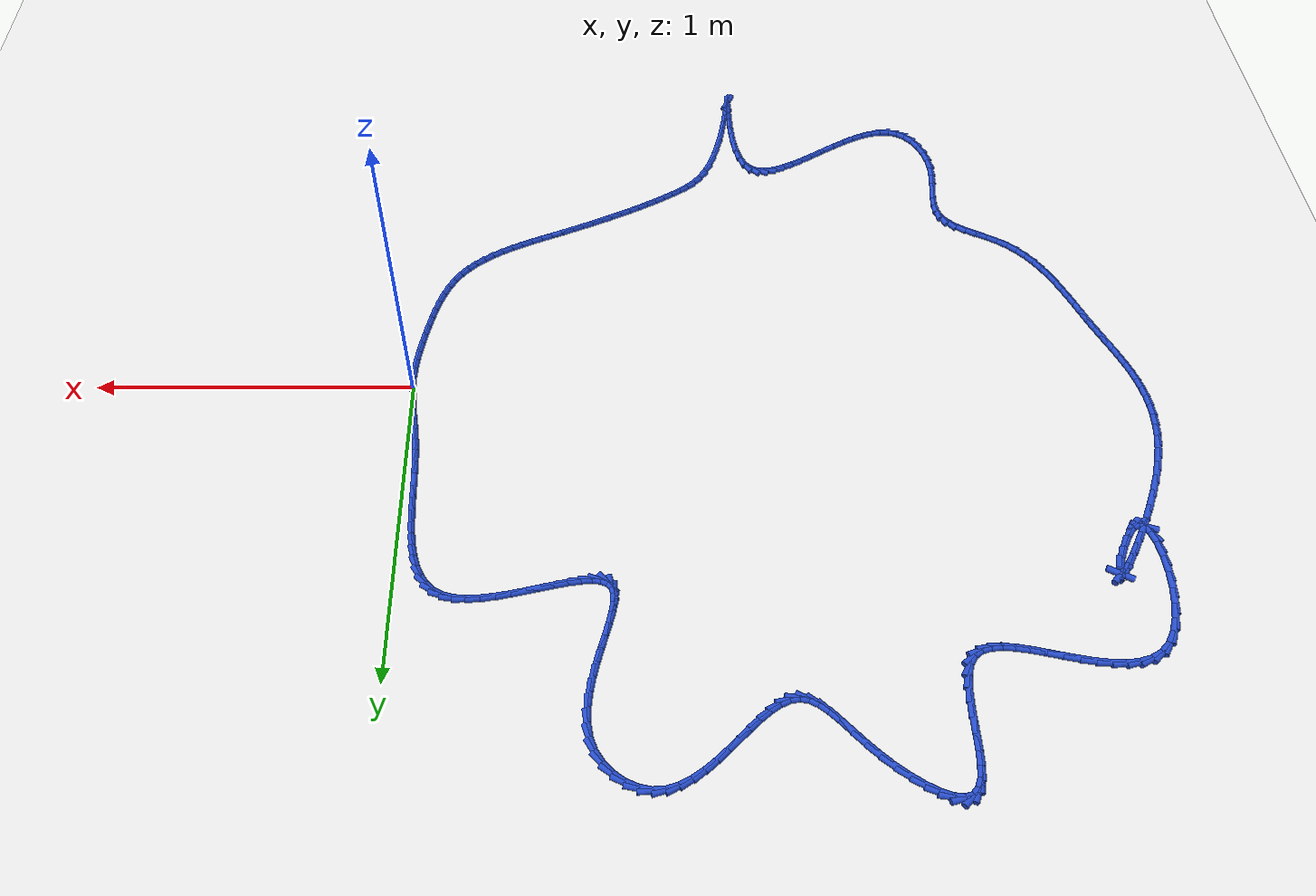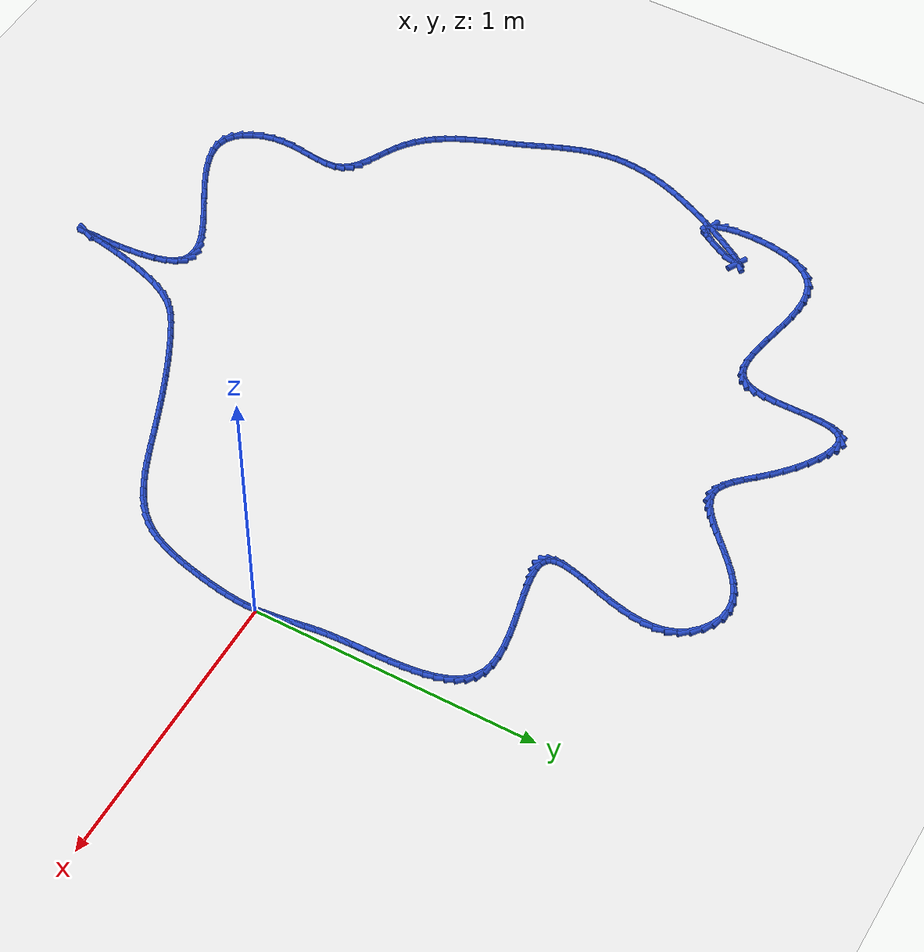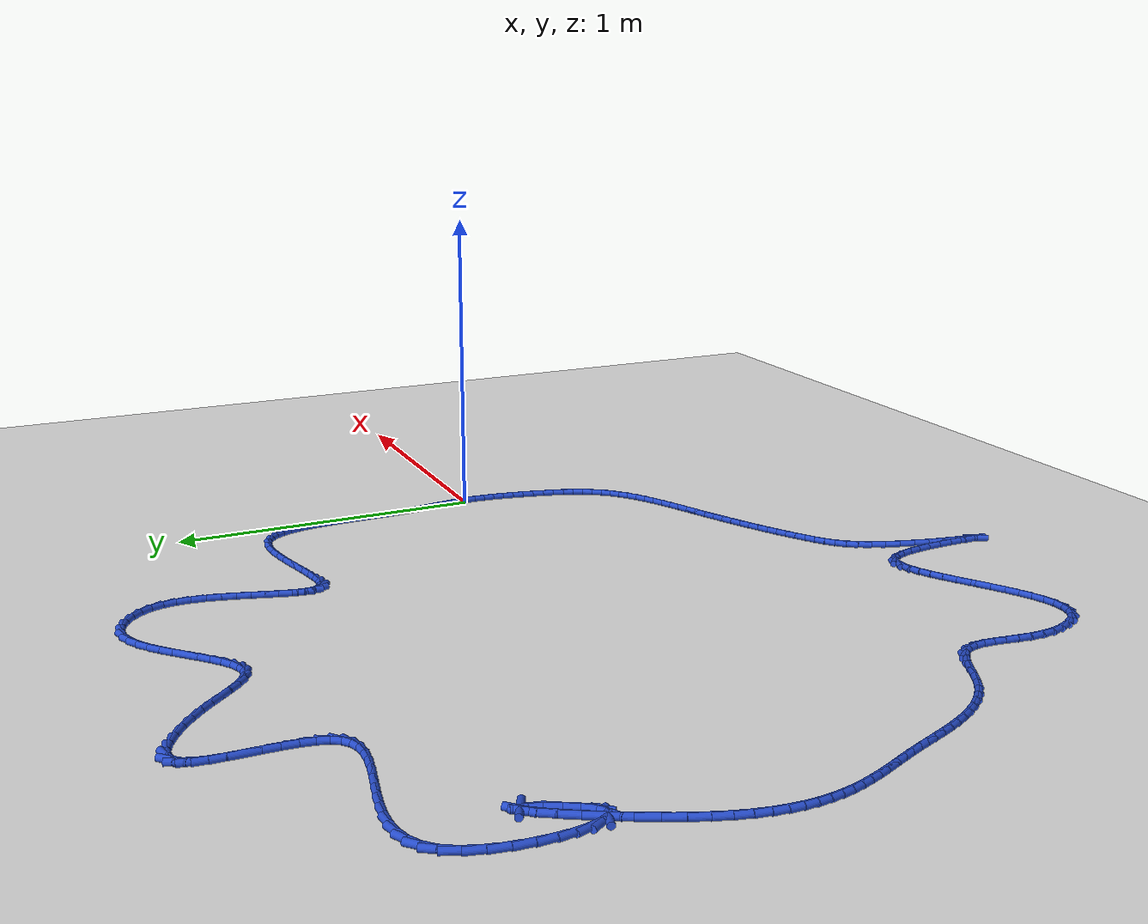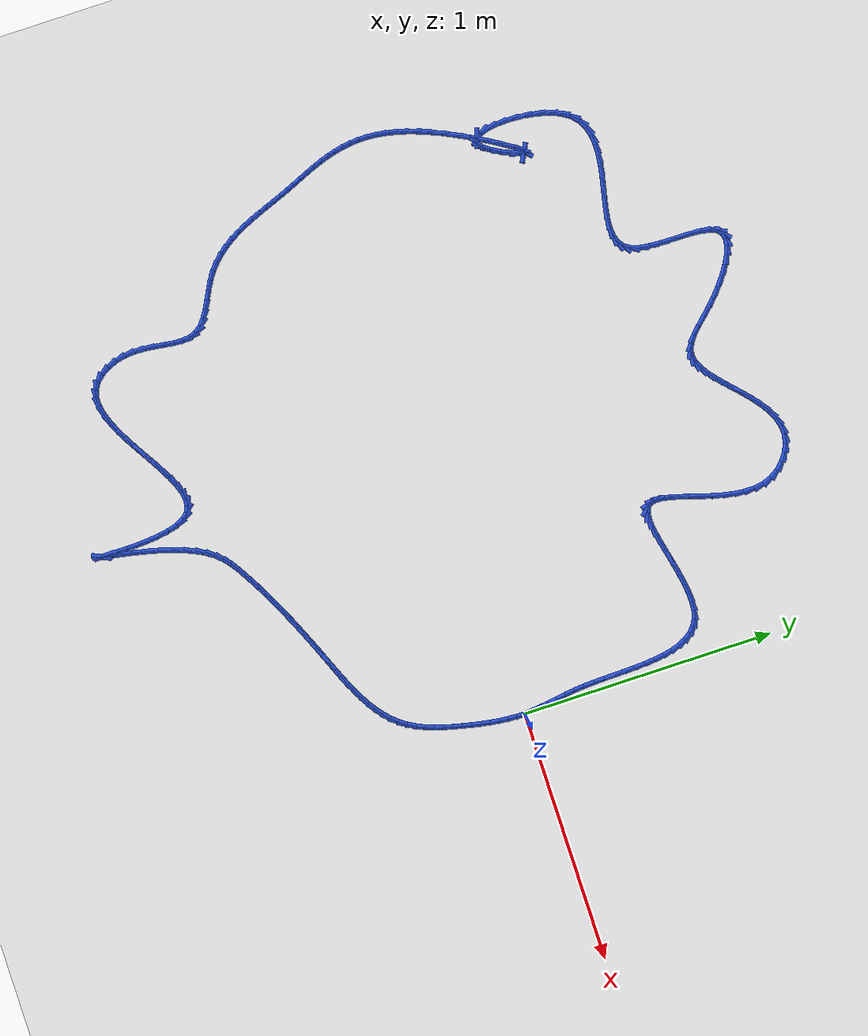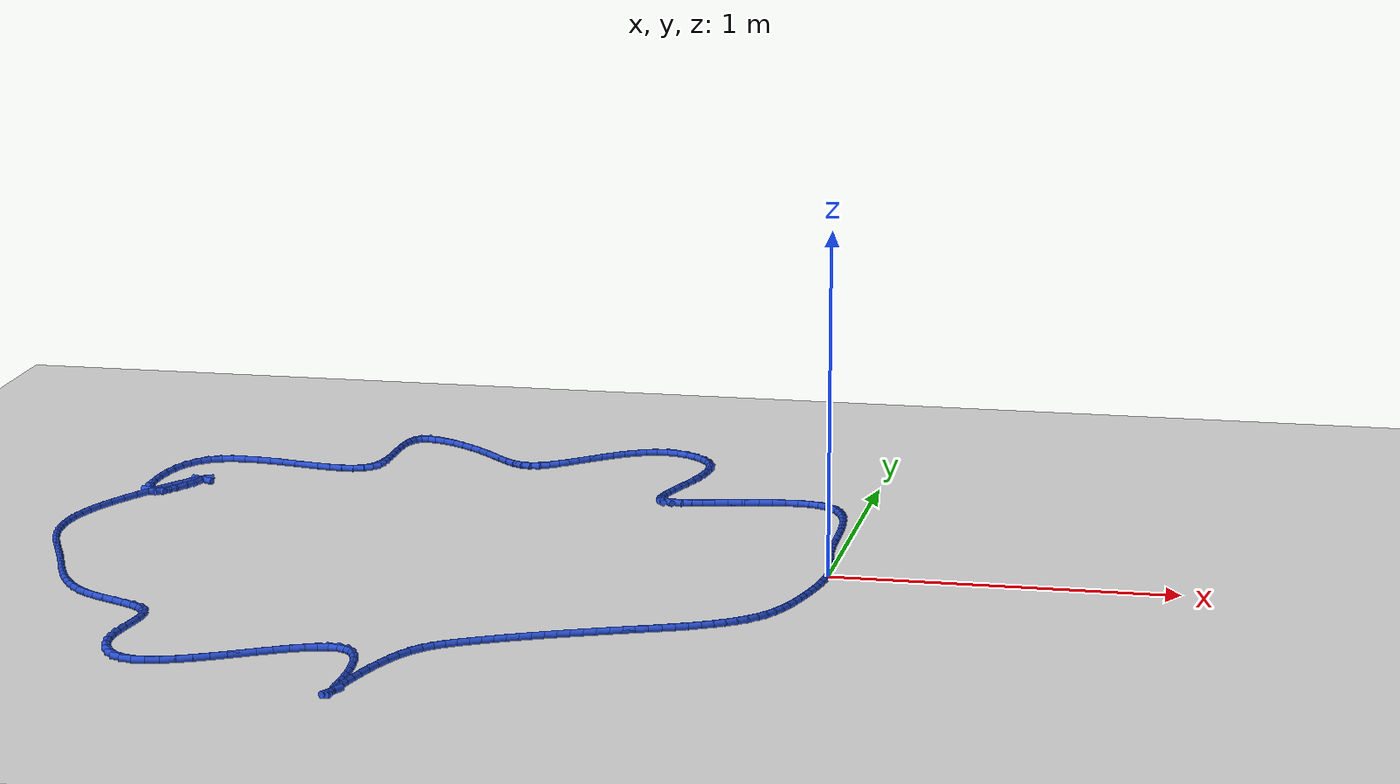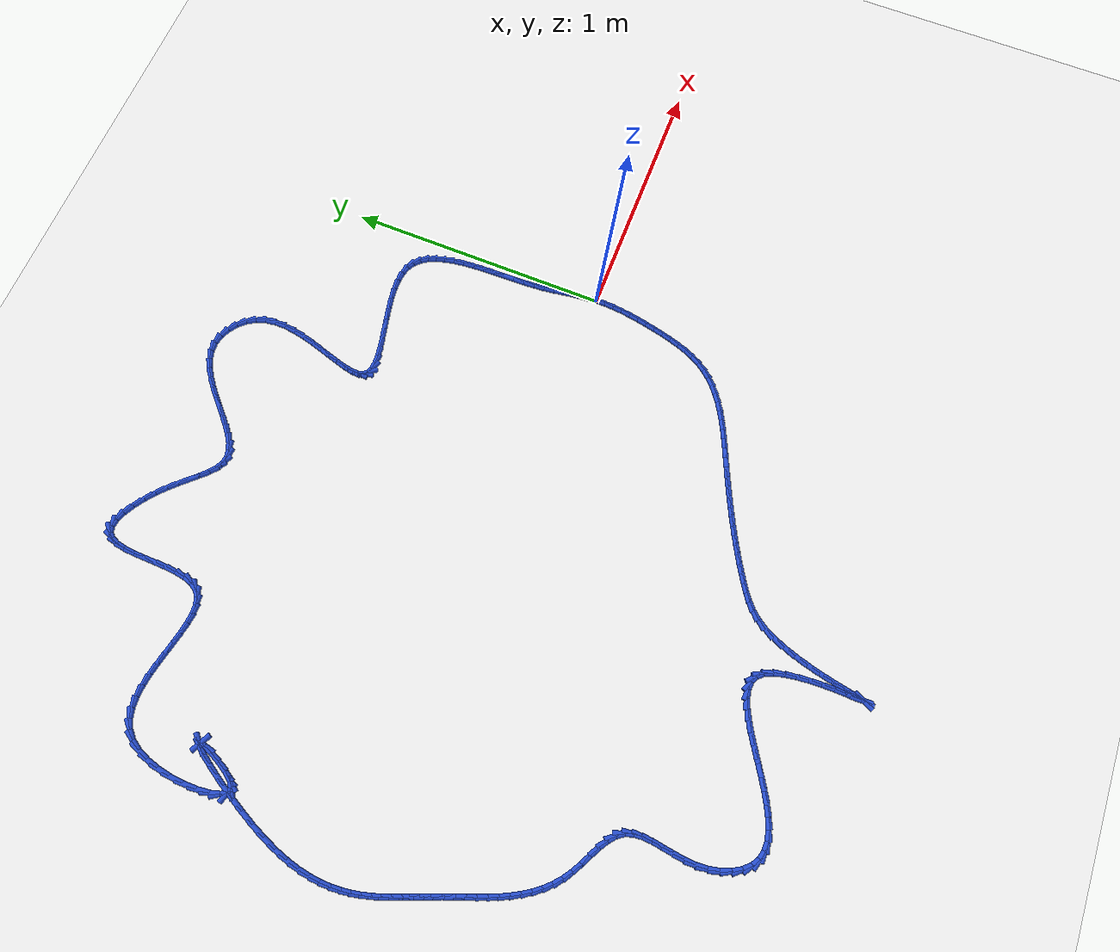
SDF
<sdf version="1.6">
 <world name="default">
  <light name="sun" type="directional">
   <pose>0 0 10 0 -0 0</pose>
   <diffuse>0.8 0.8 0.8 1</diffuse>
   <specular>0.2 0.2 0.2 1</specular>
   <attenuation>
    <range>1000</range>
    <constant>0.9</constant>
    <linear>0.01</linear>
    <quadratic>0.001</quadratic>
   </attenuation>
   <direction>-0.5 0.1 -0.9</direction>
  </light>
  <model name="ground_plane">
   <static>1</static>
   <link name="link">
    <collision name="collision">
     <geometry><plane><normal>0 0 1</normal><size>100 100</size></plane></geometry>
     <surface><friction><ode><mu>100</mu><mu2>50</mu2></ode></friction></surface>
    </collision>
    <visual name="visual">
     <cast_shadows>0</cast_shadows>
     <geometry><plane><normal>0 0 1</normal><size>100 100</size></plane></geometry>
     <material>
      <script><uri>file://media/materials/scripts/gazebo.material</uri><name>Gazebo/WhiteGlow</name></script>
     </material>
    </visual>
   </link>
  </model>
  <gravity>0 0 -9.8</gravity>
  <magnetic_field>6e-06 2.3e-05 -4.2e-05</magnetic_field>
  <atmosphere type="adiabatic"/>
  <physics name="default_physics" default="0" type="ode">
   <max_step_size>0.001</max_step_size>
   <real_time_factor>1</real_time_factor>
   <real_time_update_rate>1000</real_time_update_rate>
  </physics>
  <scene><ambient>0.4 0.4 0.4 1</ambient><background>0.7 0.7 0.7 1</background><shadows>1</shadows></scene>
  <spherical_coordinates>
   <surface_model>EARTH_WGS84</surface_model>
   <latitude_deg>0</latitude_deg>
   <longitude_deg>0</longitude_deg>
   <elevation>0</elevation>
   <heading_deg>0</heading_deg>
  </spherical_coordinates>
  <model name="line">
   <link name="link_0">
    <pose>-1.734723475976807e-17 1.0408340855860843e-16 0.01 0 1.57 -1.5083408288933977</pose>
    <collision name="collision">
     <geometry><cylinder><radius>0.01</radius><length>0.08</length></cylinder></geometry>
    </collision>
    <visual name="visual">
     <material>
      <script><name>Gazebo/Blue</name><uri>file://media/materials/scripts/gazebo.material</uri></script>
     </material>
     <geometry><cylinder><radius>0.01</radius><length>0.08</length></cylinder></geometry>
    </visual>
   </link>
   <link name="link_1">
    <pose>-0.0021196836067384752 0.033894963377618756 0.01 0 1.57 -1.461341418618367</pose>
    <collision name="collision">
     <geometry><cylinder><radius>0.01</radius><length>0.08</length></cylinder></geometry>
    </collision>
    <visual name="visual">
     <material>
      <script><name>Gazebo/Blue</name><uri>file://media/materials/scripts/gazebo.material</uri></script>
     </material>
     <geometry><cylinder><radius>0.01</radius><length>0.08</length></cylinder></geometry>
    </visual>
   </link>
   <link name="link_2">
    <pose>-0.005830443476863865 0.06766164698499161 0.01 0 1.57 -1.4313954396183446</pose>
    <collision name="collision">
     <geometry><cylinder><radius>0.01</radius><length>0.08</length></cylinder></geometry>
    </collision>
    <visual name="visual">
     <material>
      <script><name>Gazebo/Blue</name><uri>file://media/materials/scripts/gazebo.material</uri></script>
     </material>
     <geometry><cylinder><radius>0.01</radius><length>0.08</length></cylinder></geometry>
    </visual>
   </link>
   <link name="link_3">
    <pose>-0.01060383328601112 0.10168173086542234 0.01 0 1.57 -1.4188233202473002</pose>
    <collision name="collision">
     <geometry><cylinder><radius>0.01</radius><length>0.08</length></cylinder></geometry>
    </collision>
    <visual name="visual">
     <material>
      <script><name>Gazebo/Blue</name><uri>file://media/materials/scripts/gazebo.material</uri></script>
     </material>
     <geometry><cylinder><radius>0.01</radius><length>0.08</length></cylinder></geometry>
    </visual>
   </link>
   <link name="link_4">
    <pose>-0.01591140670981516 0.13633689506221444 0.01 0 1.57 -1.4229340475392616</pose>
    <collision name="collision">
     <geometry><cylinder><radius>0.01</radius><length>0.08</length></cylinder></geometry>
    </collision>
    <visual name="visual">
     <material>
      <script><name>Gazebo/Blue</name><uri>file://media/materials/scripts/gazebo.material</uri></script>
     </material>
     <geometry><cylinder><radius>0.01</radius><length>0.08</length></cylinder></geometry>
    </visual>
   </link>
   <link name="link_5">
    <pose>-0.021224717423910914 0.1720088196186716 0.01 0 1.57 -1.4422786424298313</pose>
    <collision name="collision">
     <geometry><cylinder><radius>0.01</radius><length>0.08</length></cylinder></geometry>
    </collision>
    <visual name="visual">
     <material>
      <script><name>Gazebo/Blue</name><uri>file://media/materials/scripts/gazebo.material</uri></script>
     </material>
     <geometry><cylinder><radius>0.01</radius><length>0.08</length></cylinder></geometry>
    </visual>
   </link>
   <link name="link_6">
    <pose>-0.026015319103933298 0.2090791845780972 0.01 0 1.57 -1.4747929241966398</pose>
    <collision name="collision">
     <geometry><cylinder><radius>0.01</radius><length>0.08</length></cylinder></geometry>
    </collision>
    <visual name="visual">
     <material>
      <script><name>Gazebo/Blue</name><uri>file://media/materials/scripts/gazebo.material</uri></script>
     </material>
     <geometry><cylinder><radius>0.01</radius><length>0.08</length></cylinder></geometry>
    </visual>
   </link>
   <link name="link_7">
    <pose>-0.02975644251791767 0.2479280451275408 0.01 0 1.57 -1.5106430984727284</pose>
    <collision name="collision">
     <geometry><cylinder><radius>0.01</radius><length>0.08</length></cylinder></geometry>
    </collision>
    <visual name="visual">
     <material>
      <script><name>Gazebo/Blue</name><uri>file://media/materials/scripts/gazebo.material</uri></script>
     </material>
     <geometry><cylinder><radius>0.01</radius><length>0.08</length></cylinder></geometry>
    </visual>
   </link>
   <link name="link_8">
    <pose>-0.03220934392028913 0.2886564020543827 0.01 0 1.57 -1.5342893860453386</pose>
    <collision name="collision">
     <geometry><cylinder><radius>0.01</radius><length>0.08</length></cylinder></geometry>
    </collision>
    <visual name="visual">
     <material>
      <script><name>Gazebo/Blue</name><uri>file://media/materials/scripts/gazebo.material</uri></script>
     </material>
     <geometry><cylinder><radius>0.01</radius><length>0.08</length></cylinder></geometry>
    </visual>
   </link>
   <link name="link_9">
    <pose>-0.033747541319173534 0.3307720644175201 0.01 0 1.57 -1.5457556233718104</pose>
    <collision name="collision">
     <geometry><cylinder><radius>0.01</radius><length>0.08</length></cylinder></geometry>
    </collision>
    <visual name="visual">
     <material>
      <script><name>Gazebo/Blue</name><uri>file://media/materials/scripts/gazebo.material</uri></script>
     </material>
     <geometry><cylinder><radius>0.01</radius><length>0.08</length></cylinder></geometry>
    </visual>
   </link>
   <link name="link_10">
    <pose>-0.034822885776311055 0.37370694805013344 0.01 0 1.57 -1.5461557800907932</pose>
    <collision name="collision">
     <geometry><cylinder><radius>0.01</radius><length>0.08</length></cylinder></geometry>
    </collision>
    <visual name="visual">
     <material>
      <script><name>Gazebo/Blue</name><uri>file://media/materials/scripts/gazebo.material</uri></script>
     </material>
     <geometry><cylinder><radius>0.01</radius><length>0.08</length></cylinder></geometry>
    </visual>
   </link>
   <link name="link_11">
    <pose>-0.035887228353441936 0.41689296878540383 0.01 0 1.57 -1.5356993781176984</pose>
    <collision name="collision">
     <geometry><cylinder><radius>0.01</radius><length>0.08</length></cylinder></geometry>
    </collision>
    <visual name="visual">
     <material>
      <script><name>Gazebo/Blue</name><uri>file://media/materials/scripts/gazebo.material</uri></script>
     </material>
     <geometry><cylinder><radius>0.01</radius><length>0.08</length></cylinder></geometry>
    </visual>
   </link>
   <link name="link_12">
    <pose>-0.03739242011230638 0.4597620424565119 0.01 0 1.57 -1.5137439419873586</pose>
    <collision name="collision">
     <geometry><cylinder><radius>0.01</radius><length>0.08</length></cylinder></geometry>
    </collision>
    <visual name="visual">
     <material>
      <script><name>Gazebo/Blue</name><uri>file://media/materials/scripts/gazebo.material</uri></script>
     </material>
     <geometry><cylinder><radius>0.01</radius><length>0.08</length></cylinder></geometry>
    </visual>
   </link>
   <link name="link_13">
    <pose>-0.039790312114644594 0.5017460848966384 0.01 0 1.57 -1.4787219078508933</pose>
    <collision name="collision">
     <geometry><cylinder><radius>0.01</radius><length>0.08</length></cylinder></geometry>
    </collision>
    <visual name="visual">
     <material>
      <script><name>Gazebo/Blue</name><uri>file://media/materials/scripts/gazebo.material</uri></script>
     </material>
     <geometry><cylinder><radius>0.01</radius><length>0.08</length></cylinder></geometry>
    </visual>
   </link>
   <link name="link_14">
    <pose>-0.04353275542219681 0.5422770119389643 0.01 0 1.57 -1.4279462167485715</pose>
    <collision name="collision">
     <geometry><cylinder><radius>0.01</radius><length>0.08</length></cylinder></geometry>
    </collision>
    <visual name="visual">
     <material>
      <script><name>Gazebo/Blue</name><uri>file://media/materials/scripts/gazebo.material</uri></script>
     </material>
     <geometry><cylinder><radius>0.01</radius><length>0.08</length></cylinder></geometry>
    </visual>
   </link>
   <link name="link_15">
    <pose>-0.04907160109670318 0.5807867394166697 0.01 0 1.57 -1.3573123811966512</pose>
    <collision name="collision">
     <geometry><cylinder><radius>0.01</radius><length>0.08</length></cylinder></geometry>
    </collision>
    <visual name="visual">
     <material>
      <script><name>Gazebo/Blue</name><uri>file://media/materials/scripts/gazebo.material</uri></script>
     </material>
     <geometry><cylinder><radius>0.01</radius><length>0.08</length></cylinder></geometry>
    </visual>
   </link>
   <link name="link_16">
    <pose>-0.05685870019990401 0.6167071831629366 0.01 0 1.57 -1.261009788469272</pose>
    <collision name="collision">
     <geometry><cylinder><radius>0.01</radius><length>0.08</length></cylinder></geometry>
    </collision>
    <visual name="visual">
     <material>
      <script><name>Gazebo/Blue</name><uri>file://media/materials/scripts/gazebo.material</uri></script>
     </material>
     <geometry><cylinder><radius>0.01</radius><length>0.08</length></cylinder></geometry>
    </visual>
   </link>
   <link name="link_17">
    <pose>-0.06734590379353944 0.6494702590109447 0.01 0 1.57 -1.1316759051255703</pose>
    <collision name="collision">
     <geometry><cylinder><radius>0.01</radius><length>0.08</length></cylinder></geometry>
    </collision>
    <visual name="visual">
     <material>
      <script><name>Gazebo/Blue</name><uri>file://media/materials/scripts/gazebo.material</uri></script>
     </material>
     <geometry><cylinder><radius>0.01</radius><length>0.08</length></cylinder></geometry>
    </visual>
   </link>
   <link name="link_18">
    <pose>-0.0809850629393497 0.6785078827938752 0.01 0 1.57 -0.9621862711258534</pose>
    <collision name="collision">
     <geometry><cylinder><radius>0.01</radius><length>0.08</length></cylinder></geometry>
    </collision>
    <visual name="visual">
     <material>
      <script><name>Gazebo/Blue</name><uri>file://media/materials/scripts/gazebo.material</uri></script>
     </material>
     <geometry><cylinder><radius>0.01</radius><length>0.08</length></cylinder></geometry>
    </visual>
   </link>
   <link name="link_19">
    <pose>-0.09822802869907502 0.7032519703449092 0.01 0 1.57 -0.7510232009037348</pose>
    <collision name="collision">
     <geometry><cylinder><radius>0.01</radius><length>0.08</length></cylinder></geometry>
    </collision>
    <visual name="visual">
     <material>
      <script><name>Gazebo/Blue</name><uri>file://media/materials/scripts/gazebo.material</uri></script>
     </material>
     <geometry><cylinder><radius>0.01</radius><length>0.08</length></cylinder></geometry>
    </visual>
   </link>
   <link name="link_20">
    <pose>-0.11952665213445557 0.7231344374972271 0.01 0 1.57 -0.5105275131438748</pose>
    <collision name="collision">
     <geometry><cylinder><radius>0.01</radius><length>0.08</length></cylinder></geometry>
    </collision>
    <visual name="visual">
     <material>
      <script><name>Gazebo/Blue</name><uri>file://media/materials/scripts/gazebo.material</uri></script>
     </material>
     <geometry><cylinder><radius>0.01</radius><length>0.08</length></cylinder></geometry>
    </visual>
   </link>
   <link name="link_21">
    <pose>-0.14533278430723157 0.7375872000840092 0.01 0 1.57 -0.2709992494954977</pose>
    <collision name="collision">
     <geometry><cylinder><radius>0.01</radius><length>0.08</length></cylinder></geometry>
    </collision>
    <visual name="visual">
     <material>
      <script><name>Gazebo/Blue</name><uri>file://media/materials/scripts/gazebo.material</uri></script>
     </material>
     <geometry><cylinder><radius>0.01</radius><length>0.08</length></cylinder></geometry>
    </visual>
   </link>
   <link name="link_22">
    <pose>-0.1760303442376547 0.746116032730849 0.01 0 1.57 -0.08513310534744274</pose>
    <collision name="collision">
     <geometry><cylinder><radius>0.01</radius><length>0.08</length></cylinder></geometry>
    </collision>
    <visual name="visual">
     <material>
      <script><name>Gazebo/Blue</name><uri>file://media/materials/scripts/gazebo.material</uri></script>
     </material>
     <geometry><cylinder><radius>0.01</radius><length>0.08</length></cylinder></geometry>
    </visual>
   </link>
   <link name="link_23">
    <pose>-0.21118520508179212 0.7491161265793403 0.01 0 1.57 0.039958045719969366</pose>
    <collision name="collision">
     <geometry><cylinder><radius>0.01</radius><length>0.08</length></cylinder></geometry>
    </collision>
    <visual name="visual">
     <material>
      <script><name>Gazebo/Blue</name><uri>file://media/materials/scripts/gazebo.material</uri></script>
     </material>
     <geometry><cylinder><radius>0.01</radius><length>0.08</length></cylinder></geometry>
    </visual>
   </link>
   <link name="link_24">
    <pose>-0.2498216942836033 0.7475714657979832 0.01 0 1.57 0.12323756267443166</pose>
    <collision name="collision">
     <geometry><cylinder><radius>0.01</radius><length>0.08</length></cylinder></geometry>
    </collision>
    <visual name="visual">
     <material>
      <script><name>Gazebo/Blue</name><uri>file://media/materials/scripts/gazebo.material</uri></script>
     </material>
     <geometry><cylinder><radius>0.01</radius><length>0.08</length></cylinder></geometry>
    </visual>
   </link>
   <link name="link_25">
    <pose>-0.2909544740078793 0.7424765430845653 0.01 0 1.57 0.17752093928847582</pose>
    <collision name="collision">
     <geometry><cylinder><radius>0.01</radius><length>0.08</length></cylinder></geometry>
    </collision>
    <visual name="visual">
     <material>
      <script><name>Gazebo/Blue</name><uri>file://media/materials/scripts/gazebo.material</uri></script>
     </material>
     <geometry><cylinder><radius>0.01</radius><length>0.08</length></cylinder></geometry>
    </visual>
   </link>
   <link name="link_26">
    <pose>-0.3335982064194116 0.7348258511368757 0.01 0 1.57 0.21023814794837684</pose>
    <collision name="collision">
     <geometry><cylinder><radius>0.01</radius><length>0.08</length></cylinder></geometry>
    </collision>
    <visual name="visual">
     <material>
      <script><name>Gazebo/Blue</name><uri>file://media/materials/scripts/gazebo.material</uri></script>
     </material>
     <geometry><cylinder><radius>0.01</radius><length>0.08</length></cylinder></geometry>
    </visual>
   </link>
   <link name="link_27">
    <pose>-0.37676755368299153 0.725613882652703 0.01 0 1.57 0.2250794534777034</pose>
    <collision name="collision">
     <geometry><cylinder><radius>0.01</radius><length>0.08</length></cylinder></geometry>
    </collision>
    <visual name="visual">
     <material>
      <script><name>Gazebo/Blue</name><uri>file://media/materials/scripts/gazebo.material</uri></script>
     </material>
     <geometry><cylinder><radius>0.01</radius><length>0.08</length></cylinder></geometry>
    </visual>
   </link>
   <link name="link_28">
    <pose>-0.41947717796341 0.7158351303298354 0.01 0 1.57 0.22284819515604448</pose>
    <collision name="collision">
     <geometry><cylinder><radius>0.01</radius><length>0.08</length></cylinder></geometry>
    </collision>
    <visual name="visual">
     <material>
      <script><name>Gazebo/Blue</name><uri>file://media/materials/scripts/gazebo.material</uri></script>
     </material>
     <geometry><cylinder><radius>0.01</radius><length>0.08</length></cylinder></geometry>
    </visual>
   </link>
   <link name="link_29">
    <pose>-0.46074174142545843 0.7064840868660615 0.01 0 1.57 0.20140368319027765</pose>
    <collision name="collision">
     <geometry><cylinder><radius>0.01</radius><length>0.08</length></cylinder></geometry>
    </collision>
    <visual name="visual">
     <material>
      <script><name>Gazebo/Blue</name><uri>file://media/materials/scripts/gazebo.material</uri></script>
     </material>
     <geometry><cylinder><radius>0.01</radius><length>0.08</length></cylinder></geometry>
    </visual>
   </link>
   <link name="link_30">
    <pose>-0.49957590623392817 0.6985552449591703 0.01 0 1.57 0.15439084470876607</pose>
    <collision name="collision">
     <geometry><cylinder><radius>0.01</radius><length>0.08</length></cylinder></geometry>
    </collision>
    <visual name="visual">
     <material>
      <script><name>Gazebo/Blue</name><uri>file://media/materials/scripts/gazebo.material</uri></script>
     </material>
     <geometry><cylinder><radius>0.01</radius><length>0.08</length></cylinder></geometry>
    </visual>
   </link>
   <link name="link_31">
    <pose>-0.5349943345536103 0.6930430973069497 0.01 0 1.57 0.06763170143833858</pose>
    <collision name="collision">
     <geometry><cylinder><radius>0.01</radius><length>0.08</length></cylinder></geometry>
    </collision>
    <visual name="visual">
     <material>
      <script><name>Gazebo/Blue</name><uri>file://media/materials/scripts/gazebo.material</uri></script>
     </material>
     <geometry><cylinder><radius>0.01</radius><length>0.08</length></cylinder></geometry>
    </visual>
   </link>
   <link name="link_32">
    <pose>-0.5660116885492963 0.6909421366071886 0.01 0 1.57 -0.08967822274300016</pose>
    <collision name="collision">
     <geometry><cylinder><radius>0.01</radius><length>0.08</length></cylinder></geometry>
    </collision>
    <visual name="visual">
     <material>
      <script><name>Gazebo/Blue</name><uri>file://media/materials/scripts/gazebo.material</uri></script>
     </material>
     <geometry><cylinder><radius>0.01</radius><length>0.08</length></cylinder></geometry>
    </visual>
   </link>
   <link name="link_33">
    <pose>-0.5916426303857771 0.6932468555576756 0.01 0 1.57 -0.38056074144833524</pose>
    <collision name="collision">
     <geometry><cylinder><radius>0.01</radius><length>0.08</length></cylinder></geometry>
    </collision>
    <visual name="visual">
     <material>
      <script><name>Gazebo/Blue</name><uri>file://media/materials/scripts/gazebo.material</uri></script>
     </material>
     <geometry><cylinder><radius>0.01</radius><length>0.08</length></cylinder></geometry>
    </visual>
   </link>
   <link name="link_34">
    <pose>-0.6109018222278444 0.7009517468561992 0.01 0 1.57 -0.862504595825327</pose>
    <collision name="collision">
     <geometry><cylinder><radius>0.01</radius><length>0.08</length></cylinder></geometry>
    </collision>
    <visual name="visual">
     <material>
      <script><name>Gazebo/Blue</name><uri>file://media/materials/scripts/gazebo.material</uri></script>
     </material>
     <geometry><cylinder><radius>0.01</radius><length>0.08</length></cylinder></geometry>
    </visual>
   </link>
   <link name="link_35">
    <pose>-0.6229069722507989 0.7149672416532962 0.01 0 1.57 -1.3241362118176287</pose>
    <collision name="collision">
     <geometry><cylinder><radius>0.01</radius><length>0.08</length></cylinder></geometry>
    </collision>
    <visual name="visual">
     <material>
      <script><name>Gazebo/Blue</name><uri>file://media/materials/scripts/gazebo.material</uri></script>
     </material>
     <geometry><cylinder><radius>0.01</radius><length>0.08</length></cylinder></geometry>
    </visual>
   </link>
   <link name="link_36">
    <pose>-0.6280021634322428 0.7352033348586289 0.01 0 1.57 1.5449077284649313</pose>
    <collision name="collision">
     <geometry><cylinder><radius>0.01</radius><length>0.08</length></cylinder></geometry>
    </collision>
    <visual name="visual">
     <material>
      <script><name>Gazebo/Blue</name><uri>file://media/materials/scripts/gazebo.material</uri></script>
     </material>
     <geometry><cylinder><radius>0.01</radius><length>0.08</length></cylinder></geometry>
    </visual>
   </link>
   <link name="link_37">
    <pose>-0.6273364176967755 0.760913378655054 0.01 0 1.57 1.3994939330093321</pose>
    <collision name="collision">
     <geometry><cylinder><radius>0.01</radius><length>0.08</length></cylinder></geometry>
    </collision>
    <visual name="visual">
     <material>
      <script><name>Gazebo/Blue</name><uri>file://media/materials/scripts/gazebo.material</uri></script>
     </material>
     <geometry><cylinder><radius>0.01</radius><length>0.08</length></cylinder></geometry>
    </visual>
   </link>
   <link name="link_38">
    <pose>-0.6220728031550834 0.7913392668086541 0.01 0 1.57 1.3230136876789107</pose>
    <collision name="collision">
     <geometry><cylinder><radius>0.01</radius><length>0.08</length></cylinder></geometry>
    </collision>
    <visual name="visual">
     <material>
      <script><name>Gazebo/Blue</name><uri>file://media/materials/scripts/gazebo.material</uri></script>
     </material>
     <geometry><cylinder><radius>0.01</radius><length>0.08</length></cylinder></geometry>
    </visual>
   </link>
   <link name="link_39">
    <pose>-0.6133743879178521 0.8257228930855103 0.01 0 1.57 1.2867971268913088</pose>
    <collision name="collision">
     <geometry><cylinder><radius>0.01</radius><length>0.08</length></cylinder></geometry>
    </collision>
    <visual name="visual">
     <material>
      <script><name>Gazebo/Blue</name><uri>file://media/materials/scripts/gazebo.material</uri></script>
     </material>
     <geometry><cylinder><radius>0.01</radius><length>0.08</length></cylinder></geometry>
    </visual>
   </link>
   <link name="link_40">
    <pose>-0.6024042400957679 0.8633061512517048 0.01 0 1.57 1.2777042595199484</pose>
    <collision name="collision">
     <geometry><cylinder><radius>0.01</radius><length>0.08</length></cylinder></geometry>
    </collision>
    <visual name="visual">
     <material>
      <script><name>Gazebo/Blue</name><uri>file://media/materials/scripts/gazebo.material</uri></script>
     </material>
     <geometry><cylinder><radius>0.01</radius><length>0.08</length></cylinder></geometry>
    </visual>
   </link>
   <link name="link_41">
    <pose>-0.5903254277995165 0.9033309350733199 0.01 0 1.57 1.2901092063953967</pose>
    <collision name="collision">
     <geometry><cylinder><radius>0.01</radius><length>0.08</length></cylinder></geometry>
    </collision>
    <visual name="visual">
     <material>
      <script><name>Gazebo/Blue</name><uri>file://media/materials/scripts/gazebo.material</uri></script>
     </material>
     <geometry><cylinder><radius>0.01</radius><length>0.08</length></cylinder></geometry>
    </visual>
   </link>
   <link name="link_42">
    <pose>-0.5783010191397838 0.9450391383164376 0.01 0 1.57 1.3225408035875452</pose>
    <collision name="collision">
     <geometry><cylinder><radius>0.01</radius><length>0.08</length></cylinder></geometry>
    </collision>
    <visual name="visual">
     <material>
      <script><name>Gazebo/Blue</name><uri>file://media/materials/scripts/gazebo.material</uri></script>
     </material>
     <geometry><cylinder><radius>0.01</radius><length>0.08</length></cylinder></geometry>
    </visual>
   </link>
   <link name="link_43">
    <pose>-0.5674940822272564 0.9876726547471402 0.01 0 1.57 1.376407268110528</pose>
    <collision name="collision">
     <geometry><cylinder><radius>0.01</radius><length>0.08</length></cylinder></geometry>
    </collision>
    <visual name="visual">
     <material>
      <script><name>Gazebo/Blue</name><uri>file://media/materials/scripts/gazebo.material</uri></script>
     </material>
     <geometry><cylinder><radius>0.01</radius><length>0.08</length></cylinder></geometry>
    </visual>
   </link>
   <link name="link_44">
    <pose>-0.5590676851726197 1.0304733781315087 0.01 0 1.57 1.4556292413725587</pose>
    <collision name="collision">
     <geometry><cylinder><radius>0.01</radius><length>0.08</length></cylinder></geometry>
    </collision>
    <visual name="visual">
     <material>
      <script><name>Gazebo/Blue</name><uri>file://media/materials/scripts/gazebo.material</uri></script>
     </material>
     <geometry><cylinder><radius>0.01</radius><length>0.08</length></cylinder></geometry>
    </visual>
   </link>
   <link name="link_45">
    <pose>-0.5541848960865599 1.0726832022356259 0.01 0 1.57 1.5664862830328488</pose>
    <collision name="collision">
     <geometry><cylinder><radius>0.01</radius><length>0.08</length></cylinder></geometry>
    </collision>
    <visual name="visual">
     <material>
      <script><name>Gazebo/Blue</name><uri>file://media/materials/scripts/gazebo.material</uri></script>
     </material>
     <geometry><cylinder><radius>0.01</radius><length>0.08</length></cylinder></geometry>
    </visual>
   </link>
   <link name="link_46">
    <pose>-0.554008783079763 1.1135440208255738 0.01 0 1.57 -1.4249215587054873</pose>
    <collision name="collision">
     <geometry><cylinder><radius>0.01</radius><length>0.08</length></cylinder></geometry>
    </collision>
    <visual name="visual">
     <material>
      <script><name>Gazebo/Blue</name><uri>file://media/materials/scripts/gazebo.material</uri></script>
     </material>
     <geometry><cylinder><radius>0.01</radius><length>0.08</length></cylinder></geometry>
    </visual>
   </link>
   <link name="link_47">
    <pose>-0.5597024142629147 1.1522977276674342 0.01 0 1.57 -1.2300463110513864</pose>
    <collision name="collision">
     <geometry><cylinder><radius>0.01</radius><length>0.08</length></cylinder></geometry>
    </collision>
    <visual name="visual">
     <material>
      <script><name>Gazebo/Blue</name><uri>file://media/materials/scripts/gazebo.material</uri></script>
     </material>
     <geometry><cylinder><radius>0.01</radius><length>0.08</length></cylinder></geometry>
    </visual>
   </link>
   <link name="link_48">
    <pose>-0.5724277444427394 1.1881860898677867 0.01 0 1.57 -1.009454232464364</pose>
    <collision name="collision">
     <geometry><cylinder><radius>0.01</radius><length>0.08</length></cylinder></geometry>
    </collision>
    <visual name="visual">
     <material>
      <script><name>Gazebo/Blue</name><uri>file://media/materials/scripts/gazebo.material</uri></script>
     </material>
     <geometry><cylinder><radius>0.01</radius><length>0.08</length></cylinder></geometry>
    </visual>
   </link>
   <link name="link_49">
    <pose>-0.5926679500706684 1.220373650584087 0.01 0 1.57 -0.8046204868408289</pose>
    <collision name="collision">
     <geometry><cylinder><radius>0.01</radius><length>0.08</length></cylinder></geometry>
    </collision>
    <visual name="visual">
     <material>
      <script><name>Gazebo/Blue</name><uri>file://media/materials/scripts/gazebo.material</uri></script>
     </material>
     <geometry><cylinder><radius>0.01</radius><length>0.08</length></cylinder></geometry>
    </visual>
   </link>
   <link name="link_50">
    <pose>-0.6190757357491053 1.2478167019831052 0.01 0 1.57 -0.6101670155278066</pose>
    <collision name="collision">
     <geometry><cylinder><radius>0.01</radius><length>0.08</length></cylinder></geometry>
    </collision>
    <visual name="visual">
     <material>
      <script><name>Gazebo/Blue</name><uri>file://media/materials/scripts/gazebo.material</uri></script>
     </material>
     <geometry><cylinder><radius>0.01</radius><length>0.08</length></cylinder></geometry>
    </visual>
   </link>
   <link name="link_51">
    <pose>-0.6499983434442149 1.2694367840464613 0.01 0 1.57 -0.41086556855378076</pose>
    <collision name="collision">
     <geometry><cylinder><radius>0.01</radius><length>0.08</length></cylinder></geometry>
    </collision>
    <visual name="visual">
     <material>
      <script><name>Gazebo/Blue</name><uri>file://media/materials/scripts/gazebo.material</uri></script>
     </material>
     <geometry><cylinder><radius>0.01</radius><length>0.08</length></cylinder></geometry>
    </visual>
   </link>
   <link name="link_52">
    <pose>-0.6837830151221617 1.2841554367557733 0.01 0 1.57 -0.1902404863592725</pose>
    <collision name="collision">
     <geometry><cylinder><radius>0.01</radius><length>0.08</length></cylinder></geometry>
    </collision>
    <visual name="visual">
     <material>
      <script><name>Gazebo/Blue</name><uri>file://media/materials/scripts/gazebo.material</uri></script>
     </material>
     <geometry><cylinder><radius>0.01</radius><length>0.08</length></cylinder></geometry>
    </visual>
   </link>
   <link name="link_53">
    <pose>-0.7187769927491107 1.2908942000926602 0.01 0 1.57 0.058759145812935995</pose>
    <collision name="collision">
     <geometry><cylinder><radius>0.01</radius><length>0.08</length></cylinder></geometry>
    </collision>
    <visual name="visual">
     <material>
      <script><name>Gazebo/Blue</name><uri>file://media/materials/scripts/gazebo.material</uri></script>
     </material>
     <geometry><cylinder><radius>0.01</radius><length>0.08</length></cylinder></geometry>
    </visual>
   </link>
   <link name="link_54">
    <pose>-0.7535105833220984 1.2888509318835053 0.01 0 1.57 0.2857165944162569</pose>
    <collision name="collision">
     <geometry><cylinder><radius>0.01</radius><length>0.08</length></cylinder></geometry>
    </collision>
    <visual name="visual">
     <material>
      <script><name>Gazebo/Blue</name><uri>file://media/materials/scripts/gazebo.material</uri></script>
     </material>
     <geometry><cylinder><radius>0.01</radius><length>0.08</length></cylinder></geometry>
    </visual>
   </link>
   <link name="link_55">
    <pose>-0.787585847081912 1.278841191298426 0.01 0 1.57 0.4605246924555378</pose>
    <collision name="collision">
     <geometry><cylinder><radius>0.01</radius><length>0.08</length></cylinder></geometry>
    </collision>
    <visual name="visual">
     <material>
      <script><name>Gazebo/Blue</name><uri>file://media/materials/scripts/gazebo.material</uri></script>
     </material>
     <geometry><cylinder><radius>0.01</radius><length>0.08</length></cylinder></geometry>
    </visual>
   </link>
   <link name="link_56">
    <pose>-0.8209936995555409 1.262267474587205 0.01 0 1.57 0.586162431384819</pose>
    <collision name="collision">
     <geometry><cylinder><radius>0.01</radius><length>0.08</length></cylinder></geometry>
    </collision>
    <visual name="visual">
     <material>
      <script><name>Gazebo/Blue</name><uri>file://media/materials/scripts/gazebo.material</uri></script>
     </material>
     <geometry><cylinder><radius>0.01</radius><length>0.08</length></cylinder></geometry>
    </visual>
   </link>
   <link name="link_57">
    <pose>-0.8537256021502603 1.2405331019497985 0.01 0 1.57 0.6719526054823745</pose>
    <collision name="collision">
     <geometry><cylinder><radius>0.01</radius><length>0.08</length></cylinder></geometry>
    </collision>
    <visual name="visual">
     <material>
      <script><name>Gazebo/Blue</name><uri>file://media/materials/scripts/gazebo.material</uri></script>
     </material>
     <geometry><cylinder><radius>0.01</radius><length>0.08</length></cylinder></geometry>
    </visual>
   </link>
   <link name="link_58">
    <pose>-0.8857730162733456 1.2150413935861626 0.01 0 1.57 0.7261995659306844</pose>
    <collision name="collision">
     <geometry><cylinder><radius>0.01</radius><length>0.08</length></cylinder></geometry>
    </collision>
    <visual name="visual">
     <material>
      <script><name>Gazebo/Blue</name><uri>file://media/materials/scripts/gazebo.material</uri></script>
     </material>
     <geometry><cylinder><radius>0.01</radius><length>0.08</length></cylinder></geometry>
    </visual>
   </link>
   <link name="link_59">
    <pose>-0.9171274033320718 1.1871956696962538 0.01 0 1.57 0.7541816310576566</pose>
    <collision name="collision">
     <geometry><cylinder><radius>0.01</radius><length>0.08</length></cylinder></geometry>
    </collision>
    <visual name="visual">
     <material>
      <script><name>Gazebo/Blue</name><uri>file://media/materials/scripts/gazebo.material</uri></script>
     </material>
     <geometry><cylinder><radius>0.01</radius><length>0.08</length></cylinder></geometry>
    </visual>
   </link>
   <link name="link_60">
    <pose>-0.9477802247337143 1.158399250480029 0.01 0 1.57 0.7579729174065732</pose>
    <collision name="collision">
     <geometry><cylinder><radius>0.01</radius><length>0.08</length></cylinder></geometry>
    </collision>
    <visual name="visual">
     <material>
      <script><name>Gazebo/Blue</name><uri>file://media/materials/scripts/gazebo.material</uri></script>
     </material>
     <geometry><cylinder><radius>0.01</radius><length>0.08</length></cylinder></geometry>
    </visual>
   </link>
   <link name="link_61">
    <pose>-0.977722941885548 1.1300554561374438 0.01 0 1.57 0.7363237827904611</pose>
    <collision name="collision">
     <geometry><cylinder><radius>0.01</radius><length>0.08</length></cylinder></geometry>
    </collision>
    <visual name="visual">
     <material>
      <script><name>Gazebo/Blue</name><uri>file://media/materials/scripts/gazebo.material</uri></script>
     </material>
     <geometry><cylinder><radius>0.01</radius><length>0.08</length></cylinder></geometry>
    </visual>
   </link>
   <link name="link_62">
    <pose>-1.006947016194849 1.1035676068684552 0.01 0 1.57 0.6838968438230816</pose>
    <collision name="collision">
     <geometry><cylinder><radius>0.01</radius><length>0.08</length></cylinder></geometry>
    </collision>
    <visual name="visual">
     <material>
      <script><name>Gazebo/Blue</name><uri>file://media/materials/scripts/gazebo.material</uri></script>
     </material>
     <geometry><cylinder><radius>0.01</radius><length>0.08</length></cylinder></geometry>
    </visual>
   </link>
   <link name="link_63">
    <pose>-1.0354439090688916 1.080339022873019 0.01 0 1.57 0.5894613005288506</pose>
    <collision name="collision">
     <geometry><cylinder><radius>0.01</radius><length>0.08</length></cylinder></geometry>
    </collision>
    <visual name="visual">
     <material>
      <script><name>Gazebo/Blue</name><uri>file://media/materials/scripts/gazebo.material</uri></script>
     </material>
     <geometry><cylinder><radius>0.01</radius><length>0.08</length></cylinder></geometry>
    </visual>
   </link>
   <link name="link_64">
    <pose>-1.0632050819149514 1.0617730243510919 0.01 0 1.57 0.4333456037957656</pose>
    <collision name="collision">
     <geometry><cylinder><radius>0.01</radius><length>0.08</length></cylinder></geometry>
    </collision>
    <visual name="visual">
     <material>
      <script><name>Gazebo/Blue</name><uri>file://media/materials/scripts/gazebo.material</uri></script>
     </material>
     <geometry><cylinder><radius>0.01</radius><length>0.08</length></cylinder></geometry>
    </visual>
   </link>
   <link name="link_65">
    <pose>-1.0902219961403037 1.0492729315026306 0.01 0 1.57 0.18925660998806196</pose>
    <collision name="collision">
     <geometry><cylinder><radius>0.01</radius><length>0.08</length></cylinder></geometry>
    </collision>
    <visual name="visual">
     <material>
      <script><name>Gazebo/Blue</name><uri>file://media/materials/scripts/gazebo.material</uri></script>
     </material>
     <geometry><cylinder><radius>0.01</radius><length>0.08</length></cylinder></geometry>
    </visual>
   </link>
   <link name="link_66">
    <pose>-1.1164861131522235 1.0442420645275907 0.01 0 1.57 -0.146575021665601</pose>
    <collision name="collision">
     <geometry><cylinder><radius>0.01</radius><length>0.08</length></cylinder></geometry>
    </collision>
    <visual name="visual">
     <material>
      <script><name>Gazebo/Blue</name><uri>file://media/materials/scripts/gazebo.material</uri></script>
     </material>
     <geometry><cylinder><radius>0.01</radius><length>0.08</length></cylinder></geometry>
    </visual>
   </link>
   <link name="link_67">
    <pose>-1.1420036069043422 1.0480093092403648 0.01 0 1.57 -0.4587525783404024</pose>
    <collision name="collision">
     <geometry><cylinder><radius>0.01</radius><length>0.08</length></cylinder></geometry>
    </collision>
    <visual name="visual">
     <material>
      <script><name>Gazebo/Blue</name><uri>file://media/materials/scripts/gazebo.material</uri></script>
     </material>
     <geometry><cylinder><radius>0.01</radius><length>0.08</length></cylinder></geometry>
    </visual>
   </link>
   <link name="link_68">
    <pose>-1.1670790331713046 1.0603939645372567 0.01 0 1.57 -0.6561861651003267</pose>
    <collision name="collision">
     <geometry><cylinder><radius>0.01</radius><length>0.08</length></cylinder></geometry>
    </collision>
    <visual name="visual">
     <material>
      <script><name>Gazebo/Blue</name><uri>file://media/materials/scripts/gazebo.material</uri></script>
     </material>
     <geometry><cylinder><radius>0.01</radius><length>0.08</length></cylinder></geometry>
    </visual>
   </link>
   <link name="link_69">
    <pose>-1.1922946631569908 1.0798102987483564 0.01 0 1.57 -0.7629444473544437</pose>
    <collision name="collision">
     <geometry><cylinder><radius>0.01</radius><length>0.08</length></cylinder></geometry>
    </collision>
    <visual name="visual">
     <material>
      <script><name>Gazebo/Blue</name><uri>file://media/materials/scripts/gazebo.material</uri></script>
     </material>
     <geometry><cylinder><radius>0.01</radius><length>0.08</length></cylinder></geometry>
    </visual>
   </link>
   <link name="link_70">
    <pose>-1.218243340656762 1.1046190908667255 0.01 0 1.57 -0.8084517191448768</pose>
    <collision name="collision">
     <geometry><cylinder><radius>0.01</radius><length>0.08</length></cylinder></geometry>
    </collision>
    <visual name="visual">
     <material>
      <script><name>Gazebo/Blue</name><uri>file://media/materials/scripts/gazebo.material</uri></script>
     </material>
     <geometry><cylinder><radius>0.01</radius><length>0.08</length></cylinder></geometry>
    </visual>
   </link>
   <link name="link_71">
    <pose>-1.245517909465978 1.1331811198854238 0.01 0 1.57 -0.8101593806659703</pose>
    <collision name="collision">
     <geometry><cylinder><radius>0.01</radius><length>0.08</length></cylinder></geometry>
    </collision>
    <visual name="visual">
     <material>
      <script><name>Gazebo/Blue</name><uri>file://media/materials/scripts/gazebo.material</uri></script>
     </material>
     <geometry><cylinder><radius>0.01</radius><length>0.08</length></cylinder></geometry>
    </visual>
   </link>
   <link name="link_72">
    <pose>-1.2747112133799994 1.163857164797513 0.01 0 1.57 -0.7765861091051673</pose>
    <collision name="collision">
     <geometry><cylinder><radius>0.01</radius><length>0.08</length></cylinder></geometry>
    </collision>
    <visual name="visual">
     <material>
      <script><name>Gazebo/Blue</name><uri>file://media/materials/scripts/gazebo.material</uri></script>
     </material>
     <geometry><cylinder><radius>0.01</radius><length>0.08</length></cylinder></geometry>
    </visual>
   </link>
   <link name="link_73">
    <pose>-1.306415970015183 1.1950080200310216 0.01 0 1.57 -0.7177834358554924</pose>
    <collision name="collision">
     <geometry><cylinder><radius>0.01</radius><length>0.08</length></cylinder></geometry>
    </collision>
    <visual name="visual">
     <material>
      <script><name>Gazebo/Blue</name><uri>file://media/materials/scripts/gazebo.material</uri></script>
     </material>
     <geometry><cylinder><radius>0.01</radius><length>0.08</length></cylinder></geometry>
    </visual>
   </link>
   <link name="link_74">
    <pose>-1.3408159598698612 1.2250445036392608 0.01 0 1.57 -0.6527471059041948</pose>
    <collision name="collision">
     <geometry><cylinder><radius>0.01</radius><length>0.08</length></cylinder></geometry>
    </collision>
    <visual name="visual">
     <material>
      <script><name>Gazebo/Blue</name><uri>file://media/materials/scripts/gazebo.material</uri></script>
     </material>
     <geometry><cylinder><radius>0.01</radius><length>0.08</length></cylinder></geometry>
    </visual>
   </link>
   <link name="link_75">
    <pose>-1.3767772297744654 1.2525386267106566 0.01 0 1.57 -0.5778486185933497</pose>
    <collision name="collision">
     <geometry><cylinder><radius>0.01</radius><length>0.08</length></cylinder></geometry>
    </collision>
    <visual name="visual">
     <material>
      <script><name>Gazebo/Blue</name><uri>file://media/materials/scripts/gazebo.material</uri></script>
     </material>
     <geometry><cylinder><radius>0.01</radius><length>0.08</length></cylinder></geometry>
    </visual>
   </link>
   <link name="link_76">
    <pose>-1.4129009139773259 1.2760948060193875 0.01 0 1.57 -0.48135170137967137</pose>
    <collision name="collision">
     <geometry><cylinder><radius>0.01</radius><length>0.08</length></cylinder></geometry>
    </collision>
    <visual name="visual">
     <material>
      <script><name>Gazebo/Blue</name><uri>file://media/materials/scripts/gazebo.material</uri></script>
     </material>
     <geometry><cylinder><radius>0.01</radius><length>0.08</length></cylinder></geometry>
    </visual>
   </link>
   <link name="link_77">
    <pose>-1.4477881467267752 1.2943174583396329 0.01 0 1.57 -0.342336333454044</pose>
    <collision name="collision">
     <geometry><cylinder><radius>0.01</radius><length>0.08</length></cylinder></geometry>
    </collision>
    <visual name="visual">
     <material>
      <script><name>Gazebo/Blue</name><uri>file://media/materials/scripts/gazebo.material</uri></script>
     </material>
     <geometry><cylinder><radius>0.01</radius><length>0.08</length></cylinder></geometry>
    </visual>
   </link>
   <link name="link_78">
    <pose>-1.4800400622711452 1.3058110004455716 0.01 0 1.57 -0.11882522096740321</pose>
    <collision name="collision">
     <geometry><cylinder><radius>0.01</radius><length>0.08</length></cylinder></geometry>
    </collision>
    <visual name="visual">
     <material>
      <script><name>Gazebo/Blue</name><uri>file://media/materials/scripts/gazebo.material</uri></script>
     </material>
     <geometry><cylinder><radius>0.01</radius><length>0.08</length></cylinder></geometry>
    </visual>
   </link>
   <link name="link_79">
    <pose>-1.5082577948587668 1.3091798491113833 0.01 0 1.57 0.2636939724423228</pose>
    <collision name="collision">
     <geometry><cylinder><radius>0.01</radius><length>0.08</length></cylinder></geometry>
    </collision>
    <visual name="visual">
     <material>
      <script><name>Gazebo/Blue</name><uri>file://media/materials/scripts/gazebo.material</uri></script>
     </material>
     <geometry><cylinder><radius>0.01</radius><length>0.08</length></cylinder></geometry>
    </visual>
   </link>
   <link name="link_80">
    <pose>-1.5310424787379726 1.3030284211112466 0.01 0 1.57 0.7930607881551159</pose>
    <collision name="collision">
     <geometry><cylinder><radius>0.01</radius><length>0.08</length></cylinder></geometry>
    </collision>
    <visual name="visual">
     <material>
      <script><name>Gazebo/Blue</name><uri>file://media/materials/scripts/gazebo.material</uri></script>
     </material>
     <geometry><cylinder><radius>0.01</radius><length>0.08</length></cylinder></geometry>
    </visual>
   </link>
   <link name="link_81">
    <pose>-1.5473813077872067 1.2864372569419997 0.01 0 1.57 1.1793538248620565</pose>
    <collision name="collision">
     <geometry><cylinder><radius>0.01</radius><length>0.08</length></cylinder></geometry>
    </collision>
    <visual name="visual">
     <material>
      <script><name>Gazebo/Blue</name><uri>file://media/materials/scripts/gazebo.material</uri></script>
     </material>
     <geometry><cylinder><radius>0.01</radius><length>0.08</length></cylinder></geometry>
    </visual>
   </link>
   <link name="link_82">
    <pose>-1.5580216276266965 1.2606576757428825 0.01 0 1.57 1.385898772386969</pose>
    <collision name="collision">
     <geometry><cylinder><radius>0.01</radius><length>0.08</length></cylinder></geometry>
    </collision>
    <visual name="visual">
     <material>
      <script><name>Gazebo/Blue</name><uri>file://media/materials/scripts/gazebo.material</uri></script>
     </material>
     <geometry><cylinder><radius>0.01</radius><length>0.08</length></cylinder></geometry>
    </visual>
   </link>
   <link name="link_83">
    <pose>-1.5642121401841587 1.2275593146871413 0.01 0 1.57 1.4933989534422432</pose>
    <collision name="collision">
     <geometry><cylinder><radius>0.01</radius><length>0.08</length></cylinder></geometry>
    </collision>
    <visual name="visual">
     <material>
      <script><name>Gazebo/Blue</name><uri>file://media/materials/scripts/gazebo.material</uri></script>
     </material>
     <geometry><cylinder><radius>0.01</radius><length>0.08</length></cylinder></geometry>
    </visual>
   </link>
   <link name="link_84">
    <pose>-1.5672015838978188 1.189011855976093 0.01 0 1.57 1.5461824935037016</pose>
    <collision name="collision">
     <geometry><cylinder><radius>0.01</radius><length>0.08</length></cylinder></geometry>
    </collision>
    <visual name="visual">
     <material>
      <script><name>Gazebo/Blue</name><uri>file://media/materials/scripts/gazebo.material</uri></script>
     </material>
     <geometry><cylinder><radius>0.01</radius><length>0.08</length></cylinder></geometry>
    </visual>
   </link>
   <link name="link_85">
    <pose>-1.5682386972059044 1.1468849818110531 0.01 0 1.57 1.5631881900068427</pose>
    <collision name="collision">
     <geometry><cylinder><radius>0.01</radius><length>0.08</length></cylinder></geometry>
    </collision>
    <visual name="visual">
     <material>
      <script><name>Gazebo/Blue</name><uri>file://media/materials/scripts/gazebo.material</uri></script>
     </material>
     <geometry><cylinder><radius>0.01</radius><length>0.08</length></cylinder></geometry>
    </visual>
   </link>
   <link name="link_86">
    <pose>-1.5685722185466422 1.1030483743933368 0.01 0 1.57 1.5506814797772175</pose>
    <collision name="collision">
     <geometry><cylinder><radius>0.01</radius><length>0.08</length></cylinder></geometry>
    </collision>
    <visual name="visual">
     <material>
      <script><name>Gazebo/Blue</name><uri>file://media/materials/scripts/gazebo.material</uri></script>
     </material>
     <geometry><cylinder><radius>0.01</radius><length>0.08</length></cylinder></geometry>
    </visual>
   </link>
   <link name="link_87">
    <pose>-1.5694508863582575 1.0593717159242613 0.01 0 1.57 1.5067126833468216</pose>
    <collision name="collision">
     <geometry><cylinder><radius>0.01</radius><length>0.08</length></cylinder></geometry>
    </collision>
    <visual name="visual">
     <material>
      <script><name>Gazebo/Blue</name><uri>file://media/materials/scripts/gazebo.material</uri></script>
     </material>
     <geometry><cylinder><radius>0.01</radius><length>0.08</length></cylinder></geometry>
    </visual>
   </link>
   <link name="link_88">
    <pose>-1.572123439078978 1.0177246886051428 0.01 0 1.57 1.4205330090842452</pose>
    <collision name="collision">
     <geometry><cylinder><radius>0.01</radius><length>0.08</length></cylinder></geometry>
    </collision>
    <visual name="visual">
     <material>
      <script><name>Gazebo/Blue</name><uri>file://media/materials/scripts/gazebo.material</uri></script>
     </material>
     <geometry><cylinder><radius>0.01</radius><length>0.08</length></cylinder></geometry>
    </visual>
   </link>
   <link name="link_89">
    <pose>-1.5778386151470294 0.9799769746372962 0.01 0 1.57 1.2675357836685441</pose>
    <collision name="collision">
     <geometry><cylinder><radius>0.01</radius><length>0.08</length></cylinder></geometry>
    </collision>
    <visual name="visual">
     <material>
      <script><name>Gazebo/Blue</name><uri>file://media/materials/scripts/gazebo.material</uri></script>
     </material>
     <geometry><cylinder><radius>0.01</radius><length>0.08</length></cylinder></geometry>
    </visual>
   </link>
   <link name="link_90">
    <pose>-1.5878451530006394 0.9479982562220381 0.01 0 1.57 1.0031749493380477</pose>
    <collision name="collision">
     <geometry><cylinder><radius>0.01</radius><length>0.08</length></cylinder></geometry>
    </collision>
    <visual name="visual">
     <material>
      <script><name>Gazebo/Blue</name><uri>file://media/materials/scripts/gazebo.material</uri></script>
     </material>
     <geometry><cylinder><radius>0.01</radius><length>0.08</length></cylinder></geometry>
    </visual>
   </link>
   <link name="link_91">
    <pose>-1.6033781760910821 0.92363723120992 0.01 0 1.57 0.6407603487222537</pose>
    <collision name="collision">
     <geometry><cylinder><radius>0.01</radius><length>0.08</length></cylinder></geometry>
    </collision>
    <visual name="visual">
     <material>
      <script><name>Gazebo/Blue</name><uri>file://media/materials/scripts/gazebo.material</uri></script>
     </material>
     <geometry><cylinder><radius>0.01</radius><length>0.08</length></cylinder></geometry>
    </visual>
   </link>
   <link name="link_92">
    <pose>-1.6249158930397312 0.9075759884531699 0.01 0 1.57 0.3175982405952256</pose>
    <collision name="collision">
     <geometry><cylinder><radius>0.01</radius><length>0.08</length></cylinder></geometry>
    </collision>
    <visual name="visual">
     <material>
      <script><name>Gazebo/Blue</name><uri>file://media/materials/scripts/gazebo.material</uri></script>
     </material>
     <geometry><cylinder><radius>0.01</radius><length>0.08</length></cylinder></geometry>
    </visual>
   </link>
   <link name="link_93">
    <pose>-1.6517965441296751 0.8987396194924154 0.01 0 1.57 0.08974647550719567</pose>
    <collision name="collision">
     <geometry><cylinder><radius>0.01</radius><length>0.08</length></cylinder></geometry>
    </collision>
    <visual name="visual">
     <material>
      <script><name>Gazebo/Blue</name><uri>file://media/materials/scripts/gazebo.material</uri></script>
     </material>
     <geometry><cylinder><radius>0.01</radius><length>0.08</length></cylinder></geometry>
    </visual>
   </link>
   <link name="link_94">
    <pose>-1.6832640935882182 0.8959079111514779 0.01 0 1.57 -0.055264545491171393</pose>
    <collision name="collision">
     <geometry><cylinder><radius>0.01</radius><length>0.08</length></cylinder></geometry>
    </collision>
    <visual name="visual">
     <material>
      <script><name>Gazebo/Blue</name><uri>file://media/materials/scripts/gazebo.material</uri></script>
     </material>
     <geometry><cylinder><radius>0.01</radius><length>0.08</length></cylinder></geometry>
    </visual>
   </link>
   <link name="link_95">
    <pose>-1.7185625056426617 0.8978606502541779 0.01 0 1.57 -0.14279288857099598</pose>
    <collision name="collision">
     <geometry><cylinder><radius>0.01</radius><length>0.08</length></cylinder></geometry>
    </collision>
    <visual name="visual">
     <material>
      <script><name>Gazebo/Blue</name><uri>file://media/materials/scripts/gazebo.material</uri></script>
     </material>
     <geometry><cylinder><radius>0.01</radius><length>0.08</length></cylinder></geometry>
    </visual>
   </link>
   <link name="link_96">
    <pose>-1.7569357445203089 0.903377623624336 0.01 0 1.57 -0.19083191138974856</pose>
    <collision name="collision">
     <geometry><cylinder><radius>0.01</radius><length>0.08</length></cylinder></geometry>
    </collision>
    <visual name="visual">
     <material>
      <script><name>Gazebo/Blue</name><uri>file://media/materials/scripts/gazebo.material</uri></script>
     </material>
     <geometry><cylinder><radius>0.01</radius><length>0.08</length></cylinder></geometry>
    </visual>
   </link>
   <link name="link_97">
    <pose>-1.7976277744484623 0.9112386180857729 0.01 0 1.57 -0.2095135632527881</pose>
    <collision name="collision">
     <geometry><cylinder><radius>0.01</radius><length>0.08</length></cylinder></geometry>
    </collision>
    <visual name="visual">
     <material>
      <script><name>Gazebo/Blue</name><uri>file://media/materials/scripts/gazebo.material</uri></script>
     </material>
     <geometry><cylinder><radius>0.01</radius><length>0.08</length></cylinder></geometry>
    </visual>
   </link>
   <link name="link_98">
    <pose>-1.8398825596544262 0.9202234204623096 0.01 0 1.57 -0.20355295743199653</pose>
    <collision name="collision">
     <geometry><cylinder><radius>0.01</radius><length>0.08</length></cylinder></geometry>
    </collision>
    <visual name="visual">
     <material>
      <script><name>Gazebo/Blue</name><uri>file://media/materials/scripts/gazebo.material</uri></script>
     </material>
     <geometry><cylinder><radius>0.01</radius><length>0.08</length></cylinder></geometry>
    </visual>
   </link>
   <link name="link_99">
    <pose>-1.8829440643655035 0.9291118175777673 0.01 0 1.57 -0.17385654352929056</pose>
    <collision name="collision">
     <geometry><cylinder><radius>0.01</radius><length>0.08</length></cylinder></geometry>
    </collision>
    <visual name="visual">
     <material>
      <script><name>Gazebo/Blue</name><uri>file://media/materials/scripts/gazebo.material</uri></script>
     </material>
     <geometry><cylinder><radius>0.01</radius><length>0.08</length></cylinder></geometry>
    </visual>
   </link>
   <link name="link_100">
    <pose>-1.9260562528089957 0.9366835962559659 0.01 0 1.57 -0.11817638044137264</pose>
    <collision name="collision">
     <geometry><cylinder><radius>0.01</radius><length>0.08</length></cylinder></geometry>
    </collision>
    <visual name="visual">
     <material>
      <script><name>Gazebo/Blue</name><uri>file://media/materials/scripts/gazebo.material</uri></script>
     </material>
     <geometry><cylinder><radius>0.01</radius><length>0.08</length></cylinder></geometry>
    </visual>
   </link>
   <link name="link_101">
    <pose>-1.968463089212206 0.9417185433207266 0.01 0 1.57 -0.031199746131370675</pose>
    <collision name="collision">
     <geometry><cylinder><radius>0.01</radius><length>0.08</length></cylinder></geometry>
    </collision>
    <visual name="visual">
     <material>
      <script><name>Gazebo/Blue</name><uri>file://media/materials/scripts/gazebo.material</uri></script>
     </material>
     <geometry><cylinder><radius>0.01</radius><length>0.08</length></cylinder></geometry>
    </visual>
   </link>
   <link name="link_102">
    <pose>-2.0094085378024387 0.9429964455958703 0.01 0 1.57 0.09523247041256058</pose>
    <collision name="collision">
     <geometry><cylinder><radius>0.01</radius><length>0.08</length></cylinder></geometry>
    </collision>
    <visual name="visual">
     <material>
      <script><name>Gazebo/Blue</name><uri>file://media/materials/scripts/gazebo.material</uri></script>
     </material>
     <geometry><cylinder><radius>0.01</radius><length>0.08</length></cylinder></geometry>
    </visual>
   </link>
   <link name="link_103">
    <pose>-2.0481365628069947 0.9392970899052171 0.01 0 1.57 0.2700379256716555</pose>
    <collision name="collision">
     <geometry><cylinder><radius>0.01</radius><length>0.08</length></cylinder></geometry>
    </collision>
    <visual name="visual">
     <material>
      <script><name>Gazebo/Blue</name><uri>file://media/materials/scripts/gazebo.material</uri></script>
     </material>
     <geometry><cylinder><radius>0.01</radius><length>0.08</length></cylinder></geometry>
    </visual>
   </link>
   <link name="link_104">
    <pose>-2.0838911284531783 0.9294002630725886 0.01 0 1.57 0.4956401666273879</pose>
    <collision name="collision">
     <geometry><cylinder><radius>0.01</radius><length>0.08</length></cylinder></geometry>
    </collision>
    <visual name="visual">
     <material>
      <script><name>Gazebo/Blue</name><uri>file://media/materials/scripts/gazebo.material</uri></script>
     </material>
     <geometry><cylinder><radius>0.01</radius><length>0.08</length></cylinder></geometry>
    </visual>
   </link>
   <link name="link_105">
    <pose>-2.115916198968291 0.9120857519218053 0.01 0 1.57 0.7557364006954953</pose>
    <collision name="collision">
     <geometry><cylinder><radius>0.01</radius><length>0.08</length></cylinder></geometry>
    </collision>
    <visual name="visual">
     <material>
      <script><name>Gazebo/Blue</name><uri>file://media/materials/scripts/gazebo.material</uri></script>
     </material>
     <geometry><cylinder><radius>0.01</radius><length>0.08</length></cylinder></geometry>
    </visual>
   </link>
   <link name="link_106">
    <pose>-2.143455738579638 0.8861333432766879 0.01 0 1.57 1.009842142570312</pose>
    <collision name="collision">
     <geometry><cylinder><radius>0.01</radius><length>0.08</length></cylinder></geometry>
    </collision>
    <visual name="visual">
     <material>
      <script><name>Gazebo/Blue</name><uri>file://media/materials/scripts/gazebo.material</uri></script>
     </material>
     <geometry><cylinder><radius>0.01</radius><length>0.08</length></cylinder></geometry>
    </visual>
   </link>
   <link name="link_107">
    <pose>-2.165809842082632 0.8505534764735079 0.01 0 1.57 1.1992103605465183</pose>
    <collision name="collision">
     <geometry><cylinder><radius>0.01</radius><length>0.08</length></cylinder></geometry>
    </collision>
    <visual name="visual">
     <material>
      <script><name>Gazebo/Blue</name><uri>file://media/materials/scripts/gazebo.material</uri></script>
     </material>
     <geometry><cylinder><radius>0.01</radius><length>0.08</length></cylinder></geometry>
    </visual>
   </link>
   <link name="link_108">
    <pose>-2.18286817100015 0.8067792466584116 0.01 0 1.57 1.3309456635427008</pose>
    <collision name="collision">
     <geometry><cylinder><radius>0.01</radius><length>0.08</length></cylinder></geometry>
    </collision>
    <visual name="visual">
     <material>
      <script><name>Gazebo/Blue</name><uri>file://media/materials/scripts/gazebo.material</uri></script>
     </material>
     <geometry><cylinder><radius>0.01</radius><length>0.08</length></cylinder></geometry>
    </visual>
   </link>
   <link name="link_109">
    <pose>-2.194872848784207 0.7576920904469814 0.01 0 1.57 1.4319288320552377</pose>
    <collision name="collision">
     <geometry><cylinder><radius>0.01</radius><length>0.08</length></cylinder></geometry>
    </collision>
    <visual name="visual">
     <material>
      <script><name>Gazebo/Blue</name><uri>file://media/materials/scripts/gazebo.material</uri></script>
     </material>
     <geometry><cylinder><radius>0.01</radius><length>0.08</length></cylinder></geometry>
    </visual>
   </link>
   <link name="link_110">
    <pose>-2.2020707378944575 0.7061929180510198 0.01 0 1.57 1.5191280137718226</pose>
    <collision name="collision">
     <geometry><cylinder><radius>0.01</radius><length>0.08</length></cylinder></geometry>
    </collision>
    <visual name="visual">
     <material>
      <script><name>Gazebo/Blue</name><uri>file://media/materials/scripts/gazebo.material</uri></script>
     </material>
     <geometry><cylinder><radius>0.01</radius><length>0.08</length></cylinder></geometry>
    </visual>
   </link>
   <link name="link_111">
    <pose>-2.204708700790558 0.6551826396823317 0.01 0 1.57 -1.5356347601986515</pose>
    <collision name="collision">
     <geometry><cylinder><radius>0.01</radius><length>0.08</length></cylinder></geometry>
    </collision>
    <visual name="visual">
     <material>
      <script><name>Gazebo/Blue</name><uri>file://media/materials/scripts/gazebo.material</uri></script>
     </material>
     <geometry><cylinder><radius>0.01</radius><length>0.08</length></cylinder></geometry>
    </visual>
   </link>
   <link name="link_112">
    <pose>-2.2030335999321657 0.6075621655527197 0.01 0 1.57 -1.4327651945533204</pose>
    <collision name="collision">
     <geometry><cylinder><radius>0.01</radius><length>0.08</length></cylinder></geometry>
    </collision>
    <visual name="visual">
     <material>
      <script><name>Gazebo/Blue</name><uri>file://media/materials/scripts/gazebo.material</uri></script>
     </material>
     <geometry><cylinder><radius>0.01</radius><length>0.08</length></cylinder></geometry>
    </visual>
   </link>
   <link name="link_113">
    <pose>-2.1972922977789344 0.566232405873987 0.01 0 1.57 -1.2816476685631835</pose>
    <collision name="collision">
     <geometry><cylinder><radius>0.01</radius><length>0.08</length></cylinder></geometry>
    </collision>
    <visual name="visual">
     <material>
      <script><name>Gazebo/Blue</name><uri>file://media/materials/scripts/gazebo.material</uri></script>
     </material>
     <geometry><cylinder><radius>0.01</radius><length>0.08</length></cylinder></geometry>
    </visual>
   </link>
   <link name="link_114">
    <pose>-2.1877316567905205 0.5340942708579366 0.01 0 1.57 -0.9908007730526</pose>
    <collision name="collision">
     <geometry><cylinder><radius>0.01</radius><length>0.08</length></cylinder></geometry>
    </collision>
    <visual name="visual">
     <material>
      <script><name>Gazebo/Blue</name><uri>file://media/materials/scripts/gazebo.material</uri></script>
     </material>
     <geometry><cylinder><radius>0.01</radius><length>0.08</length></cylinder></geometry>
    </visual>
   </link>
   <link name="link_115">
    <pose>-2.1745985394265803 0.514048670716372 0.01 0 1.57 -0.297828871578232</pose>
    <collision name="collision">
     <geometry><cylinder><radius>0.01</radius><length>0.08</length></cylinder></geometry>
    </collision>
    <visual name="visual">
     <material>
      <script><name>Gazebo/Blue</name><uri>file://media/materials/scripts/gazebo.material</uri></script>
     </material>
     <geometry><cylinder><radius>0.01</radius><length>0.08</length></cylinder></geometry>
    </visual>
   </link>
   <link name="link_116">
    <pose>-2.158139808146768 0.5089965156610964 0.01 0 1.57 0.575539429282387</pose>
    <collision name="collision">
     <geometry><cylinder><radius>0.01</radius><length>0.08</length></cylinder></geometry>
    </collision>
    <visual name="visual">
     <material>
      <script><name>Gazebo/Blue</name><uri>file://media/materials/scripts/gazebo.material</uri></script>
     </material>
     <geometry><cylinder><radius>0.01</radius><length>0.08</length></cylinder></geometry>
    </visual>
   </link>
   <link name="link_117">
    <pose>-2.138644152713646 0.5216455256316723 0.01 0 1.57 0.9259725405999097</pose>
    <collision name="collision">
     <geometry><cylinder><radius>0.01</radius><length>0.08</length></cylinder></geometry>
    </collision>
    <visual name="visual">
     <material>
      <script><name>Gazebo/Blue</name><uri>file://media/materials/scripts/gazebo.material</uri></script>
     </material>
     <geometry><cylinder><radius>0.01</radius><length>0.08</length></cylinder></geometry>
    </visual>
   </link>
   <link name="link_118">
    <pose>-2.117458596101057 0.5498152334981615 0.01 0 1.57 1.0592312059052331</pose>
    <collision name="collision">
     <geometry><cylinder><radius>0.01</radius><length>0.08</length></cylinder></geometry>
    </collision>
    <visual name="visual">
     <material>
      <script><name>Gazebo/Blue</name><uri>file://media/materials/scripts/gazebo.material</uri></script>
     </material>
     <geometry><cylinder><radius>0.01</radius><length>0.08</length></cylinder></geometry>
    </visual>
   </link>
   <link name="link_119">
    <pose>-2.0970449345344244 0.5861763020623878 0.01 0 1.57 1.1370471595797356</pose>
    <collision name="collision">
     <geometry><cylinder><radius>0.01</radius><length>0.08</length></cylinder></geometry>
    </collision>
    <visual name="visual">
     <material>
      <script><name>Gazebo/Blue</name><uri>file://media/materials/scripts/gazebo.material</uri></script>
     </material>
     <geometry><cylinder><radius>0.01</radius><length>0.08</length></cylinder></geometry>
    </visual>
   </link>
   <link name="link_120">
    <pose>-2.0799180891030438 0.6231540231316093 0.01 0 1.57 1.2100489900851161</pose>
    <collision name="collision">
     <geometry><cylinder><radius>0.01</radius><length>0.08</length></cylinder></geometry>
    </collision>
    <visual name="visual">
     <material>
      <script><name>Gazebo/Blue</name><uri>file://media/materials/scripts/gazebo.material</uri></script>
     </material>
     <geometry><cylinder><radius>0.01</radius><length>0.08</length></cylinder></geometry>
    </visual>
   </link>
   <link name="link_121">
    <pose>-2.0685929808962062 0.6531736885130833 0.01 0 1.57 1.3676111306710363</pose>
    <collision name="collision">
     <geometry><cylinder><radius>0.01</radius><length>0.08</length></cylinder></geometry>
    </collision>
    <visual name="visual">
     <material>
      <script><name>Gazebo/Blue</name><uri>file://media/materials/scripts/gazebo.material</uri></script>
     </material>
     <geometry><cylinder><radius>0.01</radius><length>0.08</length></cylinder></geometry>
    </visual>
   </link>
   <link name="link_122">
    <pose>-2.065206630940232 0.669610024974072 0.01 0 1.57 -0.47287700632164476</pose>
    <collision name="collision">
     <geometry><cylinder><radius>0.01</radius><length>0.08</length></cylinder></geometry>
    </collision>
    <visual name="visual">
     <material>
      <script><name>Gazebo/Blue</name><uri>file://media/materials/scripts/gazebo.material</uri></script>
     </material>
     <geometry><cylinder><radius>0.01</radius><length>0.08</length></cylinder></geometry>
    </visual>
   </link>
   <link name="link_123">
    <pose>-2.0695169119984214 0.6718151240860637 0.01 0 1.57 0.7624022305374293</pose>
    <collision name="collision">
     <geometry><cylinder><radius>0.01</radius><length>0.08</length></cylinder></geometry>
    </collision>
    <visual name="visual">
     <material>
      <script><name>Gazebo/Blue</name><uri>file://media/materials/scripts/gazebo.material</uri></script>
     </material>
     <geometry><cylinder><radius>0.01</radius><length>0.08</length></cylinder></geometry>
    </visual>
   </link>
   <link name="link_124">
    <pose>-2.0803581647931 0.6614613564897835 0.01 0 1.57 0.918964022365787</pose>
    <collision name="collision">
     <geometry><cylinder><radius>0.01</radius><length>0.08</length></cylinder></geometry>
    </collision>
    <visual name="visual">
     <material>
      <script><name>Gazebo/Blue</name><uri>file://media/materials/scripts/gazebo.material</uri></script>
     </material>
     <geometry><cylinder><radius>0.01</radius><length>0.08</length></cylinder></geometry>
    </visual>
   </link>
   <link name="link_125">
    <pose>-2.09656268855706 0.6402262218580093 0.01 0 1.57 0.9803543944942406</pose>
    <collision name="collision">
     <geometry><cylinder><radius>0.01</radius><length>0.08</length></cylinder></geometry>
    </collision>
    <visual name="visual">
     <material>
      <script><name>Gazebo/Blue</name><uri>file://media/materials/scripts/gazebo.material</uri></script>
     </material>
     <geometry><cylinder><radius>0.01</radius><length>0.08</length></cylinder></geometry>
    </visual>
   </link>
   <link name="link_126">
    <pose>-2.1169627825230926 0.6097872198635178 0.01 0 1.57 1.01790698449592</pose>
    <collision name="collision">
     <geometry><cylinder><radius>0.01</radius><length>0.08</length></cylinder></geometry>
    </collision>
    <visual name="visual">
     <material>
      <script><name>Gazebo/Blue</name><uri>file://media/materials/scripts/gazebo.material</uri></script>
     </material>
     <geometry><cylinder><radius>0.01</radius><length>0.08</length></cylinder></geometry>
    </visual>
   </link>
   <link name="link_127">
    <pose>-2.1403907459239893 0.5718218501790873 0.01 0 1.57 1.0473350150746992</pose>
    <collision name="collision">
     <geometry><cylinder><radius>0.01</radius><length>0.08</length></cylinder></geometry>
    </collision>
    <visual name="visual">
     <material>
      <script><name>Gazebo/Blue</name><uri>file://media/materials/scripts/gazebo.material</uri></script>
     </material>
     <geometry><cylinder><radius>0.01</radius><length>0.08</length></cylinder></geometry>
    </visual>
   </link>
   <link name="link_128">
    <pose>-2.1656788779925393 0.5280076124774945 0.01 0 1.57 1.074560547272194</pose>
    <collision name="collision">
     <geometry><cylinder><radius>0.01</radius><length>0.08</length></cylinder></geometry>
    </collision>
    <visual name="visual">
     <material>
      <script><name>Gazebo/Blue</name><uri>file://media/materials/scripts/gazebo.material</uri></script>
     </material>
     <geometry><cylinder><radius>0.01</radius><length>0.08</length></cylinder></geometry>
    </visual>
   </link>
   <link name="link_129">
    <pose>-2.191659477961537 0.48002200643151716 0.01 0 1.57 1.1029478777755743</pose>
    <collision name="collision">
     <geometry><cylinder><radius>0.01</radius><length>0.08</length></cylinder></geometry>
    </collision>
    <visual name="visual">
     <material>
      <script><name>Gazebo/Blue</name><uri>file://media/materials/scripts/gazebo.material</uri></script>
     </material>
     <geometry><cylinder><radius>0.01</radius><length>0.08</length></cylinder></geometry>
    </visual>
   </link>
   <link name="link_130">
    <pose>-2.2171648450637713 0.42954253171393236 0.01 0 1.57 1.135380522128656</pose>
    <collision name="collision">
     <geometry><cylinder><radius>0.01</radius><length>0.08</length></cylinder></geometry>
    </collision>
    <visual name="visual">
     <material>
      <script><name>Gazebo/Blue</name><uri>file://media/materials/scripts/gazebo.material</uri></script>
     </material>
     <geometry><cylinder><radius>0.01</radius><length>0.08</length></cylinder></geometry>
    </visual>
   </link>
   <link name="link_131">
    <pose>-2.241027278532035 0.3782466879975178 0.01 0 1.57 1.175374610402383</pose>
    <collision name="collision">
     <geometry><cylinder><radius>0.01</radius><length>0.08</length></cylinder></geometry>
    </collision>
    <visual name="visual">
     <material>
      <script><name>Gazebo/Blue</name><uri>file://media/materials/scripts/gazebo.material</uri></script>
     </material>
     <geometry><cylinder><radius>0.01</radius><length>0.08</length></cylinder></geometry>
    </visual>
   </link>
   <link name="link_132">
    <pose>-2.262079077599118 0.3278119749550505 0.01 0 1.57 1.227258740042573</pose>
    <collision name="collision">
     <geometry><cylinder><radius>0.01</radius><length>0.08</length></cylinder></geometry>
    </collision>
    <visual name="visual">
     <material>
      <script><name>Gazebo/Blue</name><uri>file://media/materials/scripts/gazebo.material</uri></script>
     </material>
     <geometry><cylinder><radius>0.01</radius><length>0.08</length></cylinder></geometry>
    </visual>
   </link>
   <link name="link_133">
    <pose>-2.2792659822197727 0.27976656938428474 0.01 0 1.57 1.2879487325858618</pose>
    <collision name="collision">
     <geometry><cylinder><radius>0.01</radius><length>0.08</length></cylinder></geometry>
    </collision>
    <visual name="visual">
     <material>
      <script><name>Gazebo/Blue</name><uri>file://media/materials/scripts/gazebo.material</uri></script>
     </material>
     <geometry><cylinder><radius>0.01</radius><length>0.08</length></cylinder></geometry>
    </visual>
   </link>
   <link name="link_134">
    <pose>-2.2924368088757054 0.23444992166233894 0.01 0 1.57 1.3539013147575227</pose>
    <collision name="collision">
     <geometry><cylinder><radius>0.01</radius><length>0.08</length></cylinder></geometry>
    </collision>
    <visual name="visual">
     <material>
      <script><name>Gazebo/Blue</name><uri>file://media/materials/scripts/gazebo.material</uri></script>
     </material>
     <geometry><cylinder><radius>0.01</radius><length>0.08</length></cylinder></geometry>
    </visual>
   </link>
   <link name="link_135">
    <pose>-2.301871906768418 0.19163345240353938 0.01 0 1.57 1.4243158251484722</pose>
    <collision name="collision">
     <geometry><cylinder><radius>0.01</radius><length>0.08</length></cylinder></geometry>
    </collision>
    <visual name="visual">
     <material>
      <script><name>Gazebo/Blue</name><uri>file://media/materials/scripts/gazebo.material</uri></script>
     </material>
     <geometry><cylinder><radius>0.01</radius><length>0.08</length></cylinder></geometry>
    </visual>
   </link>
   <link name="link_136">
    <pose>-2.307854304907324 0.1510850547709099 0.01 0 1.57 1.4978914984503744</pose>
    <collision name="collision">
     <geometry><cylinder><radius>0.01</radius><length>0.08</length></cylinder></geometry>
    </collision>
    <visual name="visual">
     <material>
      <script><name>Gazebo/Blue</name><uri>file://media/materials/scripts/gazebo.material</uri></script>
     </material>
     <geometry><cylinder><radius>0.01</radius><length>0.08</length></cylinder></geometry>
    </visual>
   </link>
   <link name="link_137">
    <pose>-2.3106670323018412 0.11257262192747448 0.01 0 1.57 -1.5687827852508678</pose>
    <collision name="collision">
     <geometry><cylinder><radius>0.01</radius><length>0.08</length></cylinder></geometry>
    </collision>
    <visual name="visual">
     <material>
      <script><name>Gazebo/Blue</name><uri>file://media/materials/scripts/gazebo.material</uri></script>
     </material>
     <geometry><cylinder><radius>0.01</radius><length>0.08</length></cylinder></geometry>
    </visual>
   </link>
   <link name="link_138">
    <pose>-2.310593117961384 0.07586404703625711 0.01 0 1.57 -1.4947404381292446</pose>
    <collision name="collision">
     <geometry><cylinder><radius>0.01</radius><length>0.08</length></cylinder></geometry>
    </collision>
    <visual name="visual">
     <material>
      <script><name>Gazebo/Blue</name><uri>file://media/materials/scripts/gazebo.material</uri></script>
     </material>
     <geometry><cylinder><radius>0.01</radius><length>0.08</length></cylinder></geometry>
    </visual>
   </link>
   <link name="link_139">
    <pose>-2.3079155908953695 0.04072722326028175 0.01 0 1.57 -1.4239750466662058</pose>
    <collision name="collision">
     <geometry><cylinder><radius>0.01</radius><length>0.08</length></cylinder></geometry>
    </collision>
    <visual name="visual">
     <material>
      <script><name>Gazebo/Blue</name><uri>file://media/materials/scripts/gazebo.material</uri></script>
     </material>
     <geometry><cylinder><radius>0.01</radius><length>0.08</length></cylinder></geometry>
    </visual>
   </link>
   <link name="link_140">
    <pose>-2.3029174801132126 0.006930043762571413 0.01 0 1.57 -1.3588040279641782</pose>
    <collision name="collision">
     <geometry><cylinder><radius>0.01</radius><length>0.08</length></cylinder></geometry>
    </collision>
    <visual name="visual">
     <material>
      <script><name>Gazebo/Blue</name><uri>file://media/materials/scripts/gazebo.material</uri></script>
     </material>
     <geometry><cylinder><radius>0.01</radius><length>0.08</length></cylinder></geometry>
    </visual>
   </link>
   <link name="link_141">
    <pose>-2.2958818146243307 -0.02575959829384799 0.01 0 1.57 -1.3012241214122584</pose>
    <collision name="collision">
     <geometry><cylinder><radius>0.01</radius><length>0.08</length></cylinder></geometry>
    </collision>
    <visual name="visual">
     <material>
      <script><name>Gazebo/Blue</name><uri>file://media/materials/scripts/gazebo.material</uri></script>
     </material>
     <geometry><cylinder><radius>0.01</radius><length>0.08</length></cylinder></geometry>
    </visual>
   </link>
   <link name="link_142">
    <pose>-2.287091623438139 -0.05757380974595344 0.01 0 1.57 -1.2527636687892028</pose>
    <collision name="collision">
     <geometry><cylinder><radius>0.01</radius><length>0.08</length></cylinder></geometry>
    </collision>
    <visual name="visual">
     <material>
      <script><name>Gazebo/Blue</name><uri>file://media/materials/scripts/gazebo.material</uri></script>
     </material>
     <geometry><cylinder><radius>0.01</radius><length>0.08</length></cylinder></geometry>
    </visual>
   </link>
   <link name="link_143">
    <pose>-2.2768299355640527 -0.08874469743072103 0.01 0 1.57 -1.2144425582864906</pose>
    <collision name="collision">
     <geometry><cylinder><radius>0.01</radius><length>0.08</length></cylinder></geometry>
    </collision>
    <visual name="visual">
     <material>
      <script><name>Gazebo/Blue</name><uri>file://media/materials/scripts/gazebo.material</uri></script>
     </material>
     <geometry><cylinder><radius>0.01</radius><length>0.08</length></cylinder></geometry>
    </visual>
   </link>
   <link name="link_144">
    <pose>-2.2653797800114885 -0.11950436818512672 0.01 0 1.57 -1.1868169839551235</pose>
    <collision name="collision">
     <geometry><cylinder><radius>0.01</radius><length>0.08</length></cylinder></geometry>
    </collision>
    <visual name="visual">
     <material>
      <script><name>Gazebo/Blue</name><uri>file://media/materials/scripts/gazebo.material</uri></script>
     </material>
     <geometry><cylinder><radius>0.01</radius><length>0.08</length></cylinder></geometry>
    </visual>
   </link>
   <link name="link_145">
    <pose>-2.2530241857898616 -0.15008492884614655 0.01 0 1.57 -1.1700670044027948</pose>
    <collision name="collision">
     <geometry><cylinder><radius>0.01</radius><length>0.08</length></cylinder></geometry>
    </collision>
    <visual name="visual">
     <material>
      <script><name>Gazebo/Blue</name><uri>file://media/materials/scripts/gazebo.material</uri></script>
     </material>
     <geometry><cylinder><radius>0.01</radius><length>0.08</length></cylinder></geometry>
    </visual>
   </link>
   <link name="link_146">
    <pose>-2.2400461819085886 -0.1807184862507566 0.01 0 1.57 -1.1640880836795284</pose>
    <collision name="collision">
     <geometry><cylinder><radius>0.01</radius><length>0.08</length></cylinder></geometry>
    </collision>
    <visual name="visual">
     <material>
      <script><name>Gazebo/Blue</name><uri>file://media/materials/scripts/gazebo.material</uri></script>
     </material>
     <geometry><cylinder><radius>0.01</radius><length>0.08</length></cylinder></geometry>
    </visual>
   </link>
   <link name="link_147">
    <pose>-2.2267287973770853 -0.2116371472359329 0.01 0 1.57 -1.1685622383191745</pose>
    <collision name="collision">
     <geometry><cylinder><radius>0.01</radius><length>0.08</length></cylinder></geometry>
    </collision>
    <visual name="visual">
     <material>
      <script><name>Gazebo/Blue</name><uri>file://media/materials/scripts/gazebo.material</uri></script>
     </material>
     <geometry><cylinder><radius>0.01</radius><length>0.08</length></cylinder></geometry>
    </visual>
   </link>
   <link name="link_148">
    <pose>-2.213355061204768 -0.2430730186386515 0.01 0 1.57 -1.1829165690441796</pose>
    <collision name="collision">
     <geometry><cylinder><radius>0.01</radius><length>0.08</length></cylinder></geometry>
    </collision>
    <visual name="visual">
     <material>
      <script><name>Gazebo/Blue</name><uri>file://media/materials/scripts/gazebo.material</uri></script>
     </material>
     <geometry><cylinder><radius>0.01</radius><length>0.08</length></cylinder></geometry>
    </visual>
   </link>
   <link name="link_149">
    <pose>-2.200205711708783 -0.27525617800104296 0.01 0 1.57 -1.1992089923962999</pose>
    <collision name="collision">
     <geometry><cylinder><radius>0.01</radius><length>0.08</length></cylinder></geometry>
    </collision>
    <visual name="visual">
     <material>
      <script><name>Gazebo/Blue</name><uri>file://media/materials/scripts/gazebo.material</uri></script>
     </material>
     <geometry><cylinder><radius>0.01</radius><length>0.08</length></cylinder></geometry>
    </visual>
   </link>
   <link name="link_150">
    <pose>-2.187354744870346 -0.3082335524863003 0.01 0 1.57 -1.2045259221192788</pose>
    <collision name="collision">
     <geometry><cylinder><radius>0.01</radius><length>0.08</length></cylinder></geometry>
    </collision>
    <visual name="visual">
     <material>
      <script><name>Gazebo/Blue</name><uri>file://media/materials/scripts/gazebo.material</uri></script>
     </material>
     <geometry><cylinder><radius>0.01</radius><length>0.08</length></cylinder></geometry>
    </visual>
   </link>
   <link name="link_151">
    <pose>-2.1745078398901097 -0.34172578215429184 0.01 0 1.57 -1.198051510476181</pose>
    <collision name="collision">
     <geometry><cylinder><radius>0.01</radius><length>0.08</length></cylinder></geometry>
    </collision>
    <visual name="visual">
     <material>
      <script><name>Gazebo/Blue</name><uri>file://media/materials/scripts/gazebo.material</uri></script>
     </material>
     <geometry><cylinder><radius>0.01</radius><length>0.08</length></cylinder></geometry>
    </visual>
   </link>
   <link name="link_152">
    <pose>-2.161332652240826 -0.3754198223329115 0.01 0 1.57 -1.1799957845923814</pose>
    <collision name="collision">
     <geometry><cylinder><radius>0.01</radius><length>0.08</length></cylinder></geometry>
    </collision>
    <visual name="visual">
     <material>
      <script><name>Gazebo/Blue</name><uri>file://media/materials/scripts/gazebo.material</uri></script>
     </material>
     <geometry><cylinder><radius>0.01</radius><length>0.08</length></cylinder></geometry>
    </visual>
   </link>
   <link name="link_153">
    <pose>-2.14749683739525 -0.40900262835005347 0.01 0 1.57 -1.1502659521412928</pose>
    <collision name="collision">
     <geometry><cylinder><radius>0.01</radius><length>0.08</length></cylinder></geometry>
    </collision>
    <visual name="visual">
     <material>
      <script><name>Gazebo/Blue</name><uri>file://media/materials/scripts/gazebo.material</uri></script>
     </material>
     <geometry><cylinder><radius>0.01</radius><length>0.08</length></cylinder></geometry>
    </visual>
   </link>
   <link name="link_154">
    <pose>-2.132668050826132 -0.4421611555336117 0.01 0 1.57 -1.108543814502635</pose>
    <collision name="collision">
     <geometry><cylinder><radius>0.01</radius><length>0.08</length></cylinder></geometry>
    </collision>
    <visual name="visual">
     <material>
      <script><name>Gazebo/Blue</name><uri>file://media/materials/scripts/gazebo.material</uri></script>
     </material>
     <geometry><cylinder><radius>0.01</radius><length>0.08</length></cylinder></geometry>
    </visual>
   </link>
   <link name="link_155">
    <pose>-2.116513948006227 -0.4745823592114801 0.01 0 1.57 -1.054404258741772</pose>
    <collision name="collision">
     <geometry><cylinder><radius>0.01</radius><length>0.08</length></cylinder></geometry>
    </collision>
    <visual name="visual">
     <material>
      <script><name>Gazebo/Blue</name><uri>file://media/materials/scripts/gazebo.material</uri></script>
     </material>
     <geometry><cylinder><radius>0.01</radius><length>0.08</length></cylinder></geometry>
    </visual>
   </link>
   <link name="link_156">
    <pose>-2.098702184408287 -0.5059531947115536 0.01 0 1.57 -0.9874959821421748</pose>
    <collision name="collision">
     <geometry><cylinder><radius>0.01</radius><length>0.08</length></cylinder></geometry>
    </collision>
    <visual name="visual">
     <material>
      <script><name>Gazebo/Blue</name><uri>file://media/materials/scripts/gazebo.material</uri></script>
     </material>
     <geometry><cylinder><radius>0.01</radius><length>0.08</length></cylinder></geometry>
    </visual>
   </link>
   <link name="link_157">
    <pose>-2.0789004155050663 -0.5359606173617248 0.01 0 1.57 -0.9078004519411259</pose>
    <collision name="collision">
     <geometry><cylinder><radius>0.01</radius><length>0.08</length></cylinder></geometry>
    </collision>
    <visual name="visual">
     <material>
      <script><name>Gazebo/Blue</name><uri>file://media/materials/scripts/gazebo.material</uri></script>
     </material>
     <geometry><cylinder><radius>0.01</radius><length>0.08</length></cylinder></geometry>
    </visual>
   </link>
   <link name="link_158">
    <pose>-2.056776296769317 -0.5642915824898882 0.01 0 1.57 -0.815956750216248</pose>
    <collision name="collision">
     <geometry><cylinder><radius>0.01</radius><length>0.08</length></cylinder></geometry>
    </collision>
    <visual name="visual">
     <material>
      <script><name>Gazebo/Blue</name><uri>file://media/materials/scripts/gazebo.material</uri></script>
     </material>
     <geometry><cylinder><radius>0.01</radius><length>0.08</length></cylinder></geometry>
    </visual>
   </link>
   <link name="link_159">
    <pose>-2.0319974836737917 -0.5906330454239378 0.01 0 1.57 -0.7135799469703918</pose>
    <collision name="collision">
     <geometry><cylinder><radius>0.01</radius><length>0.08</length></cylinder></geometry>
    </collision>
    <visual name="visual">
     <material>
      <script><name>Gazebo/Blue</name><uri>file://media/materials/scripts/gazebo.material</uri></script>
     </material>
     <geometry><cylinder><radius>0.01</radius><length>0.08</length></cylinder></geometry>
    </visual>
   </link>
   <link name="link_160">
    <pose>-2.0042316316912436 -0.6146719614917677 0.01 0 1.57 -0.6041496229908968</pose>
    <collision name="collision">
     <geometry><cylinder><radius>0.01</radius><length>0.08</length></cylinder></geometry>
    </collision>
    <visual name="visual">
     <material>
      <script><name>Gazebo/Blue</name><uri>file://media/materials/scripts/gazebo.material</uri></script>
     </material>
     <geometry><cylinder><radius>0.01</radius><length>0.08</length></cylinder></geometry>
    </visual>
   </link>
   <link name="link_161">
    <pose>-1.9731716806376287 -0.6361109688576919 0.01 0 1.57 -0.5162591555220446</pose>
    <collision name="collision">
     <geometry><cylinder><radius>0.01</radius><length>0.08</length></cylinder></geometry>
    </collision>
    <visual name="visual">
     <material>
      <script><name>Gazebo/Blue</name><uri>file://media/materials/scripts/gazebo.material</uri></script>
     </material>
     <geometry><cylinder><radius>0.01</radius><length>0.08</length></cylinder></geometry>
    </visual>
   </link>
   <link name="link_162">
    <pose>-1.9394636176448856 -0.6552438416723317 0.01 0 1.57 -0.47822896128433307</pose>
    <collision name="collision">
     <geometry><cylinder><radius>0.01</radius><length>0.08</length></cylinder></geometry>
    </collision>
    <visual name="visual">
     <material>
      <script><name>Gazebo/Blue</name><uri>file://media/materials/scripts/gazebo.material</uri></script>
     </material>
     <geometry><cylinder><radius>0.01</radius><length>0.08</length></cylinder></geometry>
    </visual>
   </link>
   <link name="link_163">
    <pose>-1.904974457245998 -0.673121707079092 0.01 0 1.57 -0.4888143986917622</pose>
    <collision name="collision">
     <geometry><cylinder><radius>0.01</radius><length>0.08</length></cylinder></geometry>
    </collision>
    <visual name="visual">
     <material>
      <script><name>Gazebo/Blue</name><uri>file://media/materials/scripts/gazebo.material</uri></script>
     </material>
     <geometry><cylinder><radius>0.01</radius><length>0.08</length></cylinder></geometry>
    </visual>
   </link>
   <link name="link_164">
    <pose>-1.8716511279814088 -0.6908452595878942 0.01 0 1.57 -0.5535450240938061</pose>
    <collision name="collision">
     <geometry><cylinder><radius>0.01</radius><length>0.08</length></cylinder></geometry>
    </collision>
    <visual name="visual">
     <material>
      <script><name>Gazebo/Blue</name><uri>file://media/materials/scripts/gazebo.material</uri></script>
     </material>
     <geometry><cylinder><radius>0.01</radius><length>0.08</length></cylinder></geometry>
    </visual>
   </link>
   <link name="link_165">
    <pose>-1.841440558391559 -0.7095151937086599 0.01 0 1.57 -0.6890314597653835</pose>
    <collision name="collision">
     <geometry><cylinder><radius>0.01</radius><length>0.08</length></cylinder></geometry>
    </collision>
    <visual name="visual">
     <material>
      <script><name>Gazebo/Blue</name><uri>file://media/materials/scripts/gazebo.material</uri></script>
     </material>
     <geometry><cylinder><radius>0.01</radius><length>0.08</length></cylinder></geometry>
    </visual>
   </link>
   <link name="link_166">
    <pose>-1.8162896770168935 -0.73023220395131 0.01 0 1.57 -0.9206984109966259</pose>
    <collision name="collision">
     <geometry><cylinder><radius>0.01</radius><length>0.08</length></cylinder></geometry>
    </collision>
    <visual name="visual">
     <material>
      <script><name>Gazebo/Blue</name><uri>file://media/materials/scripts/gazebo.material</uri></script>
     </material>
     <geometry><cylinder><radius>0.01</radius><length>0.08</length></cylinder></geometry>
    </visual>
   </link>
   <link name="link_167">
    <pose>-1.7981442621510657 -0.7540964798281571 0.01 0 1.57 -1.2217710058525422</pose>
    <collision name="collision">
     <geometry><cylinder><radius>0.01</radius><length>0.08</length></cylinder></geometry>
    </collision>
    <visual name="visual">
     <material>
      <script><name>Gazebo/Blue</name><uri>file://media/materials/scripts/gazebo.material</uri></script>
     </material>
     <geometry><cylinder><radius>0.01</radius><length>0.08</length></cylinder></geometry>
    </visual>
   </link>
   <link name="link_168">
    <pose>-1.7880564939260735 -0.7818158907515945 0.01 0 1.57 -1.4600066014789332</pose>
    <collision name="collision">
     <geometry><cylinder><radius>0.01</radius><length>0.08</length></cylinder></geometry>
    </collision>
    <visual name="visual">
     <material>
      <script><name>Gazebo/Blue</name><uri>file://media/materials/scripts/gazebo.material</uri></script>
     </material>
     <geometry><cylinder><radius>0.01</radius><length>0.08</length></cylinder></geometry>
    </visual>
   </link>
   <link name="link_169">
    <pose>-1.7845869208988725 -0.8130043948096323 0.01 0 1.57 1.5333076621526263</pose>
    <collision name="collision">
     <geometry><cylinder><radius>0.01</radius><length>0.08</length></cylinder></geometry>
    </collision>
    <visual name="visual">
     <material>
      <script><name>Gazebo/Blue</name><uri>file://media/materials/scripts/gazebo.material</uri></script>
     </material>
     <geometry><cylinder><radius>0.01</radius><length>0.08</length></cylinder></geometry>
    </visual>
   </link>
   <link name="link_170">
    <pose>-1.7858652230584684 -0.8470867840793334 0.01 0 1.57 1.4571199654497657</pose>
    <collision name="collision">
     <geometry><cylinder><radius>0.01</radius><length>0.08</length></cylinder></geometry>
    </collision>
    <visual name="visual">
     <material>
      <script><name>Gazebo/Blue</name><uri>file://media/materials/scripts/gazebo.material</uri></script>
     </material>
     <geometry><cylinder><radius>0.01</radius><length>0.08</length></cylinder></geometry>
    </visual>
   </link>
   <link name="link_171">
    <pose>-1.7900210803938652 -0.8834878506377601 0.01 0 1.57 1.4362579694201492</pose>
    <collision name="collision">
     <geometry><cylinder><radius>0.01</radius><length>0.08</length></cylinder></geometry>
    </collision>
    <visual name="visual">
     <material>
      <script><name>Gazebo/Blue</name><uri>file://media/materials/scripts/gazebo.material</uri></script>
     </material>
     <geometry><cylinder><radius>0.01</radius><length>0.08</length></cylinder></geometry>
    </visual>
   </link>
   <link name="link_172">
    <pose>-1.7951841728940694 -0.9216323865619765 0.01 0 1.57 1.4618500855248722</pose>
    <collision name="collision">
     <geometry><cylinder><radius>0.01</radius><length>0.08</length></cylinder></geometry>
    </collision>
    <visual name="visual">
     <material>
      <script><name>Gazebo/Blue</name><uri>file://media/materials/scripts/gazebo.material</uri></script>
     </material>
     <geometry><cylinder><radius>0.01</radius><length>0.08</length></cylinder></geometry>
    </visual>
   </link>
   <link name="link_173">
    <pose>-1.7994841805480841 -0.9609451839290429 0.01 0 1.57 1.5315590040485607</pose>
    <collision name="collision">
     <geometry><cylinder><radius>0.01</radius><length>0.08</length></cylinder></geometry>
    </collision>
    <visual name="visual">
     <material>
      <script><name>Gazebo/Blue</name><uri>file://media/materials/scripts/gazebo.material</uri></script>
     </material>
     <geometry><cylinder><radius>0.01</radius><length>0.08</length></cylinder></geometry>
    </visual>
   </link>
   <link name="link_174">
    <pose>-1.8010507833449148 -1.0008510348160227 0.01 0 1.57 -1.4950420251474406</pose>
    <collision name="collision">
     <geometry><cylinder><radius>0.01</radius><length>0.08</length></cylinder></geometry>
    </collision>
    <visual name="visual">
     <material>
      <script><name>Gazebo/Blue</name><uri>file://media/materials/scripts/gazebo.material</uri></script>
     </material>
     <geometry><cylinder><radius>0.01</radius><length>0.08</length></cylinder></geometry>
    </visual>
   </link>
   <link name="link_175">
    <pose>-1.7980208798495867 -1.0407709508364438 0.01 0 1.57 -1.3506247490998928</pose>
    <collision name="collision">
     <geometry><cylinder><radius>0.01</radius><length>0.08</length></cylinder></geometry>
    </collision>
    <visual name="visual">
     <material>
      <script><name>Gazebo/Blue</name><uri>file://media/materials/scripts/gazebo.material</uri></script>
     </material>
     <geometry><cylinder><radius>0.01</radius><length>0.08</length></cylinder></geometry>
    </visual>
   </link>
   <link name="link_176">
    <pose>-1.7893037807079017 -1.0797214212024058 0.01 0 1.57 -1.2010212846220474</pose>
    <collision name="collision">
     <geometry><cylinder><radius>0.01</radius><length>0.08</length></cylinder></geometry>
    </collision>
    <visual name="visual">
     <material>
      <script><name>Gazebo/Blue</name><uri>file://media/materials/scripts/gazebo.material</uri></script>
     </material>
     <geometry><cylinder><radius>0.01</radius><length>0.08</length></cylinder></geometry>
    </visual>
   </link>
   <link name="link_177">
    <pose>-1.775257449225033 -1.1159602566081799 0.01 0 1.57 -1.0341606863862847</pose>
    <collision name="collision">
     <geometry><cylinder><radius>0.01</radius><length>0.08</length></cylinder></geometry>
    </collision>
    <visual name="visual">
     <material>
      <script><name>Gazebo/Blue</name><uri>file://media/materials/scripts/gazebo.material</uri></script>
     </material>
     <geometry><cylinder><radius>0.01</radius><length>0.08</length></cylinder></geometry>
    </visual>
   </link>
   <link name="link_178">
    <pose>-1.7563993222783485 -1.1476617493334584 0.01 0 1.57 -0.8304473702950266</pose>
    <collision name="collision">
     <geometry><cylinder><radius>0.01</radius><length>0.08</length></cylinder></geometry>
    </collision>
    <visual name="visual">
     <material>
      <script><name>Gazebo/Blue</name><uri>file://media/materials/scripts/gazebo.material</uri></script>
     </material>
     <geometry><cylinder><radius>0.01</radius><length>0.08</length></cylinder></geometry>
    </visual>
   </link>
   <link name="link_179">
    <pose>-1.7332468367452174 -1.173000191657932 0.01 0 1.57 -0.5671967575770067</pose>
    <collision name="collision">
     <geometry><cylinder><radius>0.01</radius><length>0.08</length></cylinder></geometry>
    </collision>
    <visual name="visual">
     <material>
      <script><name>Gazebo/Blue</name><uri>file://media/materials/scripts/gazebo.material</uri></script>
     </material>
     <geometry><cylinder><radius>0.01</radius><length>0.08</length></cylinder></geometry>
    </visual>
   </link>
   <link name="link_180">
    <pose>-1.70631734405298 -1.1901548361147092 0.01 0 1.57 -0.25986079799941353</pose>
    <collision name="collision">
     <geometry><cylinder><radius>0.01</radius><length>0.08</length></cylinder></geometry>
    </collision>
    <visual name="visual">
     <material>
      <script><name>Gazebo/Blue</name><uri>file://media/materials/scripts/gazebo.material</uri></script>
     </material>
     <geometry><cylinder><radius>0.01</radius><length>0.08</length></cylinder></geometry>
    </visual>
   </link>
   <link name="link_181">
    <pose>-1.6761130290681425 -1.1981853326775036 0.01 0 1.57 0.004476997973868027</pose>
    <collision name="collision">
     <geometry><cylinder><radius>0.01</radius><length>0.08</length></cylinder></geometry>
    </collision>
    <visual name="visual">
     <material>
      <script><name>Gazebo/Blue</name><uri>file://media/materials/scripts/gazebo.material</uri></script>
     </material>
     <geometry><cylinder><radius>0.01</radius><length>0.08</length></cylinder></geometry>
    </visual>
   </link>
   <link name="link_182">
    <pose>-1.6431035828927165 -1.198037548466485 0.01 0 1.57 0.19921303554239045</pose>
    <collision name="collision">
     <geometry><cylinder><radius>0.01</radius><length>0.08</length></cylinder></geometry>
    </collision>
    <visual name="visual">
     <material>
      <script><name>Gazebo/Blue</name><uri>file://media/materials/scripts/gazebo.material</uri></script>
     </material>
     <geometry><cylinder><radius>0.01</radius><length>0.08</length></cylinder></geometry>
    </visual>
   </link>
   <link name="link_183">
    <pose>-1.607754501157026 -1.1909008918089434 0.01 0 1.57 0.3344711127186619</pose>
    <collision name="collision">
     <geometry><cylinder><radius>0.01</radius><length>0.08</length></cylinder></geometry>
    </collision>
    <visual name="visual">
     <material>
      <script><name>Gazebo/Blue</name><uri>file://media/materials/scripts/gazebo.material</uri></script>
     </material>
     <geometry><cylinder><radius>0.01</radius><length>0.08</length></cylinder></geometry>
    </visual>
   </link>
   <link name="link_184">
    <pose>-1.570531279491395 -1.1779647710321675 0.01 0 1.57 0.42633220727601434</pose>
    <collision name="collision">
     <geometry><cylinder><radius>0.01</radius><length>0.08</length></cylinder></geometry>
    </collision>
    <visual name="visual">
     <material>
      <script><name>Gazebo/Blue</name><uri>file://media/materials/scripts/gazebo.material</uri></script>
     </material>
     <geometry><cylinder><radius>0.01</radius><length>0.08</length></cylinder></geometry>
    </visual>
   </link>
   <link name="link_185">
    <pose>-1.5318994135261494 -1.1604185944634484 0.01 0 1.57 0.4872020570172521</pose>
    <collision name="collision">
     <geometry><cylinder><radius>0.01</radius><length>0.08</length></cylinder></geometry>
    </collision>
    <visual name="visual">
     <material>
      <script><name>Gazebo/Blue</name><uri>file://media/materials/scripts/gazebo.material</uri></script>
     </material>
     <geometry><cylinder><radius>0.01</radius><length>0.08</length></cylinder></geometry>
    </visual>
   </link>
   <link name="link_186">
    <pose>-1.4923243988916133 -1.1394517704300746 0.01 0 1.57 0.5249767001721724</pose>
    <collision name="collision">
     <geometry><cylinder><radius>0.01</radius><length>0.08</length></cylinder></geometry>
    </collision>
    <visual name="visual">
     <material>
      <script><name>Gazebo/Blue</name><uri>file://media/materials/scripts/gazebo.material</uri></script>
     </material>
     <geometry><cylinder><radius>0.01</radius><length>0.08</length></cylinder></geometry>
    </visual>
   </link>
   <link name="link_187">
    <pose>-1.4522717312181113 -1.1162537072593364 0.01 0 1.57 0.5441001921309442</pose>
    <collision name="collision">
     <geometry><cylinder><radius>0.01</radius><length>0.08</length></cylinder></geometry>
    </collision>
    <visual name="visual">
     <material>
      <script><name>Gazebo/Blue</name><uri>file://media/materials/scripts/gazebo.material</uri></script>
     </material>
     <geometry><cylinder><radius>0.01</radius><length>0.08</length></cylinder></geometry>
    </visual>
   </link>
   <link name="link_188">
    <pose>-1.4122069061359672 -1.0920138132785226 0.01 0 1.57 0.5464383502074726</pose>
    <collision name="collision">
     <geometry><cylinder><radius>0.01</radius><length>0.08</length></cylinder></geometry>
    </collision>
    <visual name="visual">
     <material>
      <script><name>Gazebo/Blue</name><uri>file://media/materials/scripts/gazebo.material</uri></script>
     </material>
     <geometry><cylinder><radius>0.01</radius><length>0.08</length></cylinder></geometry>
    </visual>
   </link>
   <link name="link_189">
    <pose>-1.3725954192755083 -1.0679214968149242 0.01 0 1.57 0.5316270303186934</pose>
    <collision name="collision">
     <geometry><cylinder><radius>0.01</radius><length>0.08</length></cylinder></geometry>
    </collision>
    <visual name="visual">
     <material>
      <script><name>Gazebo/Blue</name><uri>file://media/materials/scripts/gazebo.material</uri></script>
     </material>
     <geometry><cylinder><radius>0.01</radius><length>0.08</length></cylinder></geometry>
    </visual>
   </link>
   <link name="link_190">
    <pose>-1.3339027662670582 -1.0451661661958307 0.01 0 1.57 0.4968425384254276</pose>
    <collision name="collision">
     <geometry><cylinder><radius>0.01</radius><length>0.08</length></cylinder></geometry>
    </collision>
    <visual name="visual">
     <material>
      <script><name>Gazebo/Blue</name><uri>file://media/materials/scripts/gazebo.material</uri></script>
     </material>
     <geometry><cylinder><radius>0.01</radius><length>0.08</length></cylinder></geometry>
    </visual>
   </link>
   <link name="link_191">
    <pose>-1.2965944427409413 -1.0249372297485306 0.01 0 1.57 0.43583564819461706</pose>
    <collision name="collision">
     <geometry><cylinder><radius>0.01</radius><length>0.08</length></cylinder></geometry>
    </collision>
    <visual name="visual">
     <material>
      <script><name>Gazebo/Blue</name><uri>file://media/materials/scripts/gazebo.material</uri></script>
     </material>
     <geometry><cylinder><radius>0.01</radius><length>0.08</length></cylinder></geometry>
    </visual>
   </link>
   <link name="link_192">
    <pose>-1.2611359443274825 -1.0084240958003148 0.01 0 1.57 0.3368847572300218</pose>
    <collision name="collision">
     <geometry><cylinder><radius>0.01</radius><length>0.08</length></cylinder></geometry>
    </collision>
    <visual name="visual">
     <material>
      <script><name>Gazebo/Blue</name><uri>file://media/materials/scripts/gazebo.material</uri></script>
     </material>
     <geometry><cylinder><radius>0.01</radius><length>0.08</length></cylinder></geometry>
    </visual>
   </link>
   <link name="link_193">
    <pose>-1.2279927666570067 -0.9968161726784726 0.01 0 1.57 0.17962632273559043</pose>
    <collision name="collision">
     <geometry><cylinder><radius>0.01</radius><length>0.08</length></cylinder></geometry>
    </collision>
    <visual name="visual">
     <material>
      <script><name>Gazebo/Blue</name><uri>file://media/materials/scripts/gazebo.material</uri></script>
     </material>
     <geometry><cylinder><radius>0.01</radius><length>0.08</length></cylinder></geometry>
    </visual>
   </link>
   <link name="link_194">
    <pose>-1.1976304053598386 -0.9913028687102932 0.01 0 1.57 -0.06520909234085456</pose>
    <collision name="collision">
     <geometry><cylinder><radius>0.01</radius><length>0.08</length></cylinder></geometry>
    </collision>
    <visual name="visual">
     <material>
      <script><name>Gazebo/Blue</name><uri>file://media/materials/scripts/gazebo.material</uri></script>
     </material>
     <geometry><cylinder><radius>0.01</radius><length>0.08</length></cylinder></geometry>
    </visual>
   </link>
   <link name="link_195">
    <pose>-1.1705143560663027 -0.9930735922230665 0.01 0 1.57 -0.4125826995164991</pose>
    <collision name="collision">
     <geometry><cylinder><radius>0.01</radius><length>0.08</length></cylinder></geometry>
    </collision>
    <visual name="visual">
     <material>
      <script><name>Gazebo/Blue</name><uri>file://media/materials/scripts/gazebo.material</uri></script>
     </material>
     <geometry><cylinder><radius>0.01</radius><length>0.08</length></cylinder></geometry>
    </visual>
   </link>
   <link name="link_196">
    <pose>-1.1471101144067237 -1.0033177515440823 0.01 0 1.57 -0.8026436570679641</pose>
    <collision name="collision">
     <geometry><cylinder><radius>0.01</radius><length>0.08</length></cylinder></geometry>
    </collision>
    <visual name="visual">
     <material>
      <script><name>Gazebo/Blue</name><uri>file://media/materials/scripts/gazebo.material</uri></script>
     </material>
     <geometry><cylinder><radius>0.01</radius><length>0.08</length></cylinder></geometry>
    </visual>
   </link>
   <link name="link_197">
    <pose>-1.1278820380798302 -1.0232207291215274 0.01 0 1.57 -1.1070997527312882</pose>
    <collision name="collision">
     <geometry><cylinder><radius>0.01</radius><length>0.08</length></cylinder></geometry>
    </collision>
    <visual name="visual">
     <material>
      <script><name>Gazebo/Blue</name><uri>file://media/materials/scripts/gazebo.material</uri></script>
     </material>
     <geometry><cylinder><radius>0.01</radius><length>0.08</length></cylinder></geometry>
    </visual>
   </link>
   <link name="link_198">
    <pose>-1.1130099518981207 -1.052961260778309 0.01 0 1.57 -1.2851180182362618</pose>
    <collision name="collision">
     <geometry><cylinder><radius>0.01</radius><length>0.08</length></cylinder></geometry>
    </collision>
    <visual name="visual">
     <material>
      <script><name>Gazebo/Blue</name><uri>file://media/materials/scripts/gazebo.material</uri></script>
     </material>
     <geometry><cylinder><radius>0.01</radius><length>0.08</length></cylinder></geometry>
    </visual>
   </link>
   <link name="link_199">
    <pose>-1.102016145087372 -1.0903917924376414 0.01 0 1.57 -1.3924838078361783</pose>
    <collision name="collision">
     <geometry><cylinder><radius>0.01</radius><length>0.08</length></cylinder></geometry>
    </collision>
    <visual name="visual">
     <material>
      <script><name>Gazebo/Blue</name><uri>file://media/materials/scripts/gazebo.material</uri></script>
     </material>
     <geometry><cylinder><radius>0.01</radius><length>0.08</length></cylinder></geometry>
    </visual>
   </link>
   <link name="link_200">
    <pose>-1.094330309286916 -1.133037169761349 0.01 0 1.57 -1.4621988073214252</pose>
    <collision name="collision">
     <geometry><cylinder><radius>0.01</radius><length>0.08</length></cylinder></geometry>
    </collision>
    <visual name="visual">
     <material>
      <script><name>Gazebo/Blue</name><uri>file://media/materials/scripts/gazebo.material</uri></script>
     </material>
     <geometry><cylinder><radius>0.01</radius><length>0.08</length></cylinder></geometry>
    </visual>
   </link>
   <link name="link_201">
    <pose>-1.0893821361360867 -1.1784222384112564 0.01 0 1.57 -1.5099549078218284</pose>
    <collision name="collision">
     <geometry><cylinder><radius>0.01</radius><length>0.08</length></cylinder></geometry>
    </collision>
    <visual name="visual">
     <material>
      <script><name>Gazebo/Blue</name><uri>file://media/materials/scripts/gazebo.material</uri></script>
     </material>
     <geometry><cylinder><radius>0.01</radius><length>0.08</length></cylinder></geometry>
    </visual>
   </link>
   <link name="link_202">
    <pose>-1.0866013172742164 -1.2240718440491876 0.01 0 1.57 -1.5435516769465956</pose>
    <collision name="collision">
     <geometry><cylinder><radius>0.01</radius><length>0.08</length></cylinder></geometry>
    </collision>
    <visual name="visual">
     <material>
      <script><name>Gazebo/Blue</name><uri>file://media/materials/scripts/gazebo.material</uri></script>
     </material>
     <geometry><cylinder><radius>0.01</radius><length>0.08</length></cylinder></geometry>
    </visual>
   </link>
   <link name="link_203">
    <pose>-1.0854175443406384 -1.267510832336968 0.01 0 1.57 -1.5667441597692473</pose>
    <collision name="collision">
     <geometry><cylinder><radius>0.01</radius><length>0.08</length></cylinder></geometry>
    </collision>
    <visual name="visual">
     <material>
      <script><name>Gazebo/Blue</name><uri>file://media/materials/scripts/gazebo.material</uri></script>
     </material>
     <geometry><cylinder><radius>0.01</radius><length>0.08</length></cylinder></geometry>
    </visual>
   </link>
   <link name="link_204">
    <pose>-1.0852605089746854 -1.3062640489364228 0.01 0 1.57 1.5613198097956762</pose>
    <collision name="collision">
     <geometry><cylinder><radius>0.01</radius><length>0.08</length></cylinder></geometry>
    </collision>
    <visual name="visual">
     <material>
      <script><name>Gazebo/Blue</name><uri>file://media/materials/scripts/gazebo.material</uri></script>
     </material>
     <geometry><cylinder><radius>0.01</radius><length>0.08</length></cylinder></geometry>
    </visual>
   </link>
   <link name="link_205">
    <pose>-1.0855599028156901 -1.3378563395093743 0.01 0 1.57 1.5623472241925498</pose>
    <collision name="collision">
     <geometry><cylinder><radius>0.01</radius><length>0.08</length></cylinder></geometry>
    </collision>
    <visual name="visual">
     <material>
      <script><name>Gazebo/Blue</name><uri>file://media/materials/scripts/gazebo.material</uri></script>
     </material>
     <geometry><cylinder><radius>0.01</radius><length>0.08</length></cylinder></geometry>
    </visual>
   </link>
   <link name="link_206">
    <pose>-1.085745417502986 -1.359812549717648 0.01 0 1.57 -1.5203960471916462</pose>
    <collision name="collision">
     <geometry><cylinder><radius>0.01</radius><length>0.08</length></cylinder></geometry>
    </collision>
    <visual name="visual">
     <material>
      <script><name>Gazebo/Blue</name><uri>file://media/materials/scripts/gazebo.material</uri></script>
     </material>
     <geometry><cylinder><radius>0.01</radius><length>0.08</length></cylinder></geometry>
    </visual>
   </link>
   <link name="link_207">
    <pose>-1.085248132235438 -1.3696709103077611 0.01 0 1.57 1.119772440966508</pose>
    <collision name="collision">
     <geometry><cylinder><radius>0.01</radius><length>0.08</length></cylinder></geometry>
    </collision>
    <visual name="visual">
     <material>
      <script><name>Gazebo/Blue</name><uri>file://media/materials/scripts/gazebo.material</uri></script>
     </material>
     <geometry><cylinder><radius>0.01</radius><length>0.08</length></cylinder></geometry>
    </visual>
   </link>
   <link name="link_208">
    <pose>-1.08364289087235 -1.3663564769589966 0.01 0 1.57 1.3814901009448788</pose>
    <collision name="collision">
     <geometry><cylinder><radius>0.01</radius><length>0.08</length></cylinder></geometry>
    </collision>
    <visual name="visual">
     <material>
      <script><name>Gazebo/Blue</name><uri>file://media/materials/scripts/gazebo.material</uri></script>
     </material>
     <geometry><cylinder><radius>0.01</radius><length>0.08</length></cylinder></geometry>
    </visual>
   </link>
   <link name="link_209">
    <pose>-1.0807716296163246 -1.3513708100348139 0.01 0 1.57 1.4009400455428023</pose>
    <collision name="collision">
     <geometry><cylinder><radius>0.01</radius><length>0.08</length></cylinder></geometry>
    </collision>
    <visual name="visual">
     <material>
      <script><name>Gazebo/Blue</name><uri>file://media/materials/scripts/gazebo.material</uri></script>
     </material>
     <geometry><cylinder><radius>0.01</radius><length>0.08</length></cylinder></geometry>
    </visual>
   </link>
   <link name="link_210">
    <pose>-1.0765053454093902 -1.3264958041468793 0.01 0 1.57 1.3970099627679942</pose>
    <collision name="collision">
     <geometry><cylinder><radius>0.01</radius><length>0.08</length></cylinder></geometry>
    </collision>
    <visual name="visual">
     <material>
      <script><name>Gazebo/Blue</name><uri>file://media/materials/scripts/gazebo.material</uri></script>
     </material>
     <geometry><cylinder><radius>0.01</radius><length>0.08</length></cylinder></geometry>
    </visual>
   </link>
   <link name="link_211">
    <pose>-1.0707150351935781 -1.2935133539068617 0.01 0 1.57 1.3836527331481097</pose>
    <collision name="collision">
     <geometry><cylinder><radius>0.01</radius><length>0.08</length></cylinder></geometry>
    </collision>
    <visual name="visual">
     <material>
      <script><name>Gazebo/Blue</name><uri>file://media/materials/scripts/gazebo.material</uri></script>
     </material>
     <geometry><cylinder><radius>0.01</radius><length>0.08</length></cylinder></geometry>
    </visual>
   </link>
   <link name="link_212">
    <pose>-1.0632716959109163 -1.2542053539264275 0.01 0 1.57 1.3634432633721643</pose>
    <collision name="collision">
     <geometry><cylinder><radius>0.01</radius><length>0.08</length></cylinder></geometry>
    </collision>
    <visual name="visual">
     <material>
      <script><name>Gazebo/Blue</name><uri>file://media/materials/scripts/gazebo.material</uri></script>
     </material>
     <geometry><cylinder><radius>0.01</radius><length>0.08</length></cylinder></geometry>
    </visual>
   </link>
   <link name="link_213">
    <pose>-1.0540463245034353 -1.2103536988172436 0.01 0 1.57 1.3362823281799938</pose>
    <collision name="collision">
     <geometry><cylinder><radius>0.01</radius><length>0.08</length></cylinder></geometry>
    </collision>
    <visual name="visual">
     <material>
      <script><name>Gazebo/Blue</name><uri>file://media/materials/scripts/gazebo.material</uri></script>
     </material>
     <geometry><cylinder><radius>0.01</radius><length>0.08</length></cylinder></geometry>
    </visual>
   </link>
   <link name="link_214">
    <pose>-1.0429099179131647 -1.1637402831909807 0.01 0 1.57 1.3007062222505306</pose>
    <collision name="collision">
     <geometry><cylinder><radius>0.01</radius><length>0.08</length></cylinder></geometry>
    </collision>
    <visual name="visual">
     <material>
      <script><name>Gazebo/Blue</name><uri>file://media/materials/scripts/gazebo.material</uri></script>
     </material>
     <geometry><cylinder><radius>0.01</radius><length>0.08</length></cylinder></geometry>
    </visual>
   </link>
   <link name="link_215">
    <pose>-1.0297334730821341 -1.1161470016593045 0.01 0 1.57 1.2538928837933083</pose>
    <collision name="collision">
     <geometry><cylinder><radius>0.01</radius><length>0.08</length></cylinder></geometry>
    </collision>
    <visual name="visual">
     <material>
      <script><name>Gazebo/Blue</name><uri>file://media/materials/scripts/gazebo.material</uri></script>
     </material>
     <geometry><cylinder><radius>0.01</radius><length>0.08</length></cylinder></geometry>
    </visual>
   </link>
   <link name="link_216">
    <pose>-1.014387986952373 -1.0693557488338832 0.01 0 1.57 1.1910585346294407</pose>
    <collision name="collision">
     <geometry><cylinder><radius>0.01</radius><length>0.08</length></cylinder></geometry>
    </collision>
    <visual name="visual">
     <material>
      <script><name>Gazebo/Blue</name><uri>file://media/materials/scripts/gazebo.material</uri></script>
     </material>
     <geometry><cylinder><radius>0.01</radius><length>0.08</length></cylinder></geometry>
    </visual>
   </link>
   <link name="link_217">
    <pose>-0.9967444564659116 -1.025148419326385 0.01 0 1.57 1.1041448831460305</pose>
    <collision name="collision">
     <geometry><cylinder><radius>0.01</radius><length>0.08</length></cylinder></geometry>
    </collision>
    <visual name="visual">
     <material>
      <script><name>Gazebo/Blue</name><uri>file://media/materials/scripts/gazebo.material</uri></script>
     </material>
     <geometry><cylinder><radius>0.01</radius><length>0.08</length></cylinder></geometry>
    </visual>
   </link>
   <link name="link_218">
    <pose>-0.976673878564779 -0.9853069077484762 0.01 0 1.57 0.9808519543670113</pose>
    <collision name="collision">
     <geometry><cylinder><radius>0.01</radius><length>0.08</length></cylinder></geometry>
    </collision>
    <visual name="visual">
     <material>
      <script><name>Gazebo/Blue</name><uri>file://media/materials/scripts/gazebo.material</uri></script>
     </material>
     <geometry><cylinder><radius>0.01</radius><length>0.08</length></cylinder></geometry>
    </visual>
   </link>
   <link name="link_219">
    <pose>-0.9540626194705556 -0.9515322988519656 0.01 0 1.57 0.8362951013649679</pose>
    <collision name="collision">
     <geometry><cylinder><radius>0.01</radius><length>0.08</length></cylinder></geometry>
    </collision>
    <visual name="visual">
     <material>
      <script><name>Gazebo/Blue</name><uri>file://media/materials/scripts/gazebo.material</uri></script>
     </material>
     <geometry><cylinder><radius>0.01</radius><length>0.08</length></cylinder></geometry>
    </visual>
   </link>
   <link name="link_220">
    <pose>-0.929106731181188 -0.9238973860880022 0.01 0 1.57 0.7074623010002005</pose>
    <collision name="collision">
     <geometry><cylinder><radius>0.01</radius><length>0.08</length></cylinder></geometry>
    </collision>
    <visual name="visual">
     <material>
      <script><name>Gazebo/Blue</name><uri>file://media/materials/scripts/gazebo.material</uri></script>
     </material>
     <geometry><cylinder><radius>0.01</radius><length>0.08</length></cylinder></geometry>
    </visual>
   </link>
   <link name="link_221">
    <pose>-0.9022894079395688 -0.9009652028374644 0.01 0 1.57 0.6105874469443884</pose>
    <collision name="collision">
     <geometry><cylinder><radius>0.01</radius><length>0.08</length></cylinder></geometry>
    </collision>
    <visual name="visual">
     <material>
      <script><name>Gazebo/Blue</name><uri>file://media/materials/scripts/gazebo.material</uri></script>
     </material>
     <geometry><cylinder><radius>0.01</radius><length>0.08</length></cylinder></geometry>
    </visual>
   </link>
   <link name="link_222">
    <pose>-0.8741046964864588 -0.8812417213269214 0.01 0 1.57 0.5547772711405596</pose>
    <collision name="collision">
     <geometry><cylinder><radius>0.01</radius><length>0.08</length></cylinder></geometry>
    </collision>
    <visual name="visual">
     <material>
      <script><name>Gazebo/Blue</name><uri>file://media/materials/scripts/gazebo.material</uri></script>
     </material>
     <geometry><cylinder><radius>0.01</radius><length>0.08</length></cylinder></geometry>
    </visual>
   </link>
   <link name="link_223">
    <pose>-0.8450462023105927 -0.8632342419303829 0.01 0 1.57 0.5317357584510772</pose>
    <collision name="collision">
     <geometry><cylinder><radius>0.01</radius><length>0.08</length></cylinder></geometry>
    </collision>
    <visual name="visual">
     <material>
      <script><name>Gazebo/Blue</name><uri>file://media/materials/scripts/gazebo.material</uri></script>
     </material>
     <geometry><cylinder><radius>0.01</radius><length>0.08</length></cylinder></geometry>
    </visual>
   </link>
   <link name="link_224">
    <pose>-0.8154777861100226 -0.8458405906208781 0.01 0 1.57 0.5139392345225913</pose>
    <collision name="collision">
     <geometry><cylinder><radius>0.01</radius><length>0.08</length></cylinder></geometry>
    </collision>
    <visual name="visual">
     <material>
      <script><name>Gazebo/Blue</name><uri>file://media/materials/scripts/gazebo.material</uri></script>
     </material>
     <geometry><cylinder><radius>0.01</radius><length>0.08</length></cylinder></geometry>
    </visual>
   </link>
   <link name="link_225">
    <pose>-0.7854536341955307 -0.8288906984290048 0.01 0 1.57 0.49731054069001546</pose>
    <collision name="collision">
     <geometry><cylinder><radius>0.01</radius><length>0.08</length></cylinder></geometry>
    </collision>
    <visual name="visual">
     <material>
      <script><name>Gazebo/Blue</name><uri>file://media/materials/scripts/gazebo.material</uri></script>
     </material>
     <geometry><cylinder><radius>0.01</radius><length>0.08</length></cylinder></geometry>
    </visual>
   </link>
   <link name="link_226">
    <pose>-0.7549827117381717 -0.8123506098476985 0.01 0 1.57 0.48185183333624654</pose>
    <collision name="collision">
     <geometry><cylinder><radius>0.01</radius><length>0.08</length></cylinder></geometry>
    </collision>
    <visual name="visual">
     <material>
      <script><name>Gazebo/Blue</name><uri>file://media/materials/scripts/gazebo.material</uri></script>
     </material>
     <geometry><cylinder><radius>0.01</radius><length>0.08</length></cylinder></geometry>
    </visual>
   </link>
   <link name="link_227">
    <pose>-0.7240739839090004 -0.7961863693698933 0.01 0 1.57 0.4675601696359078</pose>
    <collision name="collision">
     <geometry><cylinder><radius>0.01</radius><length>0.08</length></cylinder></geometry>
    </collision>
    <visual name="visual">
     <material>
      <script><name>Gazebo/Blue</name><uri>file://media/materials/scripts/gazebo.material</uri></script>
     </material>
     <geometry><cylinder><radius>0.01</radius><length>0.08</length></cylinder></geometry>
    </visual>
   </link>
   <link name="link_228">
    <pose>-0.692736415879072 -0.7803640214885249 0.01 0 1.57 0.45442823263692816</pose>
    <collision name="collision">
     <geometry><cylinder><radius>0.01</radius><length>0.08</length></cylinder></geometry>
    </collision>
    <visual name="visual">
     <material>
      <script><name>Gazebo/Blue</name><uri>file://media/materials/scripts/gazebo.material</uri></script>
     </material>
     <geometry><cylinder><radius>0.01</radius><length>0.08</length></cylinder></geometry>
    </visual>
   </link>
   <link name="link_229">
    <pose>-0.6609789728194406 -0.7648496106965277 0.01 0 1.57 0.4424450158273842</pose>
    <collision name="collision">
     <geometry><cylinder><radius>0.01</radius><length>0.08</length></cylinder></geometry>
    </collision>
    <visual name="visual">
     <material>
      <script><name>Gazebo/Blue</name><uri>file://media/materials/scripts/gazebo.material</uri></script>
     </material>
     <geometry><cylinder><radius>0.01</radius><length>0.08</length></cylinder></geometry>
    </visual>
   </link>
   <link name="link_230">
    <pose>-0.628810619901163 -0.7496091814868376 0.01 0 1.57 0.4315964557780358</pose>
    <collision name="collision">
     <geometry><cylinder><radius>0.01</radius><length>0.08</length></cylinder></geometry>
    </collision>
    <visual name="visual">
     <material>
      <script><name>Gazebo/Blue</name><uri>file://media/materials/scripts/gazebo.material</uri></script>
     </material>
     <geometry><cylinder><radius>0.01</radius><length>0.08</length></cylinder></geometry>
    </visual>
   </link>
   <link name="link_231">
    <pose>-0.5962403222952934 -0.734608778352389 0.01 0 1.57 0.42186600568672544</pose>
    <collision name="collision">
     <geometry><cylinder><radius>0.01</radius><length>0.08</length></cylinder></geometry>
    </collision>
    <visual name="visual">
     <material>
      <script><name>Gazebo/Blue</name><uri>file://media/materials/scripts/gazebo.material</uri></script>
     </material>
     <geometry><cylinder><radius>0.01</radius><length>0.08</length></cylinder></geometry>
    </visual>
   </link>
   <link name="link_232">
    <pose>-0.5632770451728865 -0.7198144457861171 0.01 0 1.57 0.41323514617133844</pose>
    <collision name="collision">
     <geometry><cylinder><radius>0.01</radius><length>0.08</length></cylinder></geometry>
    </collision>
    <visual name="visual">
     <material>
      <script><name>Gazebo/Blue</name><uri>file://media/materials/scripts/gazebo.material</uri></script>
     </material>
     <geometry><cylinder><radius>0.01</radius><length>0.08</length></cylinder></geometry>
    </visual>
   </link>
   <link name="link_233">
    <pose>-0.5299297537049977 -0.705192228280957 0.01 0 1.57 0.4056838324601998</pose>
    <collision name="collision">
     <geometry><cylinder><radius>0.01</radius><length>0.08</length></cylinder></geometry>
    </collision>
    <visual name="visual">
     <material>
      <script><name>Gazebo/Blue</name><uri>file://media/materials/scripts/gazebo.material</uri></script>
     </material>
     <geometry><cylinder><radius>0.01</radius><length>0.08</length></cylinder></geometry>
    </visual>
   </link>
   <link name="link_234">
    <pose>-0.4962074130626819 -0.6907081703298434 0.01 0 1.57 0.3991908792628699</pose>
    <collision name="collision">
     <geometry><cylinder><radius>0.01</radius><length>0.08</length></cylinder></geometry>
    </collision>
    <visual name="visual">
     <material>
      <script><name>Gazebo/Blue</name><uri>file://media/materials/scripts/gazebo.material</uri></script>
     </material>
     <geometry><cylinder><radius>0.01</radius><length>0.08</length></cylinder></geometry>
    </visual>
   </link>
   <link name="link_235">
    <pose>-0.4621189884169937 -0.6763283164257113 0.01 0 1.57 0.3940002818799265</pose>
    <collision name="collision">
     <geometry><cylinder><radius>0.01</radius><length>0.08</length></cylinder></geometry>
    </collision>
    <visual name="visual">
     <material>
      <script><name>Gazebo/Blue</name><uri>file://media/materials/scripts/gazebo.material</uri></script>
     </material>
     <geometry><cylinder><radius>0.01</radius><length>0.08</length></cylinder></geometry>
    </visual>
   </link>
   <link name="link_236">
    <pose>-0.4276833460531439 -0.6620120825470951 0.01 0 1.57 0.3942336895467431</pose>
    <collision name="collision">
     <geometry><cylinder><radius>0.01</radius><length>0.08</length></cylinder></geometry>
    </collision>
    <visual name="visual">
     <material>
      <script><name>Gazebo/Blue</name><uri>file://media/materials/scripts/gazebo.material</uri></script>
     </material>
     <geometry><cylinder><radius>0.01</radius><length>0.08</length></cylinder></geometry>
    </visual>
   </link>
   <link name="link_237">
    <pose>-0.39307510026431897 -0.647614615809711 0.01 0 1.57 0.4031352848203707</pose>
    <collision name="collision">
     <geometry><cylinder><radius>0.01</radius><length>0.08</length></cylinder></geometry>
    </collision>
    <visual name="visual">
     <material>
      <script><name>Gazebo/Blue</name><uri>file://media/materials/scripts/gazebo.material</uri></script>
     </material>
     <geometry><cylinder><radius>0.01</radius><length>0.08</length></cylinder></geometry>
    </visual>
   </link>
   <link name="link_238">
    <pose>-0.3585927692935109 -0.6329081131579471 0.01 0 1.57 0.42092614533798667</pose>
    <collision name="collision">
     <geometry><cylinder><radius>0.01</radius><length>0.08</length></cylinder></geometry>
    </collision>
    <visual name="visual">
     <material>
      <script><name>Gazebo/Blue</name><uri>file://media/materials/scripts/gazebo.material</uri></script>
     </material>
     <geometry><cylinder><radius>0.01</radius><length>0.08</length></cylinder></geometry>
    </visual>
   </link>
   <link name="link_239">
    <pose>-0.32453829905093945 -0.617662476810446 0.01 0 1.57 0.44798397071897006</pose>
    <collision name="collision">
     <geometry><cylinder><radius>0.01</radius><length>0.08</length></cylinder></geometry>
    </collision>
    <visual name="visual">
     <material>
      <script><name>Gazebo/Blue</name><uri>file://media/materials/scripts/gazebo.material</uri></script>
     </material>
     <geometry><cylinder><radius>0.01</radius><length>0.08</length></cylinder></geometry>
    </visual>
   </link>
   <link name="link_240">
    <pose>-0.2912136354468244 -0.6016476089858495 0.01 0 1.57 0.48491257346410926</pose>
    <collision name="collision">
     <geometry><cylinder><radius>0.01</radius><length>0.08</length></cylinder></geometry>
    </collision>
    <visual name="visual">
     <material>
      <script><name>Gazebo/Blue</name><uri>file://media/materials/scripts/gazebo.material</uri></script>
     </material>
     <geometry><cylinder><radius>0.01</radius><length>0.08</length></cylinder></geometry>
    </visual>
   </link>
   <link name="link_241">
    <pose>-0.2589207243913854 -0.5846334119027998 0.01 0 1.57 0.5324993611597449</pose>
    <collision name="collision">
     <geometry><cylinder><radius>0.01</radius><length>0.08</length></cylinder></geometry>
    </collision>
    <visual name="visual">
     <material>
      <script><name>Gazebo/Blue</name><uri>file://media/materials/scripts/gazebo.material</uri></script>
     </material>
     <geometry><cylinder><radius>0.01</radius><length>0.08</length></cylinder></geometry>
    </visual>
   </link>
   <link name="link_242">
    <pose>-0.2279615117948421 -0.5663897877799392 0.01 0 1.57 0.5916320526467961</pose>
    <collision name="collision">
     <geometry><cylinder><radius>0.01</radius><length>0.08</length></cylinder></geometry>
    </collision>
    <visual name="visual">
     <material>
      <script><name>Gazebo/Blue</name><uri>file://media/materials/scripts/gazebo.material</uri></script>
     </material>
     <geometry><cylinder><radius>0.01</radius><length>0.08</length></cylinder></geometry>
    </visual>
   </link>
   <link name="link_243">
    <pose>-0.1986379435674144 -0.5466866388359098 0.01 0 1.57 0.6631457641800654</pose>
    <collision name="collision">
     <geometry><cylinder><radius>0.01</radius><length>0.08</length></cylinder></geometry>
    </collision>
    <visual name="visual">
     <material>
      <script><name>Gazebo/Blue</name><uri>file://media/materials/scripts/gazebo.material</uri></script>
     </material>
     <geometry><cylinder><radius>0.01</radius><length>0.08</length></cylinder></geometry>
    </visual>
   </link>
   <link name="link_244">
    <pose>-0.17125196561932185 -0.525293867289354 0.01 0 1.57 0.7475707729629116</pose>
    <collision name="collision">
     <geometry><cylinder><radius>0.01</radius><length>0.08</length></cylinder></geometry>
    </collision>
    <visual name="visual">
     <material>
      <script><name>Gazebo/Blue</name><uri>file://media/materials/scripts/gazebo.material</uri></script>
     </material>
     <geometry><cylinder><radius>0.01</radius><length>0.08</length></cylinder></geometry>
    </visual>
   </link>
   <link name="link_245">
    <pose>-0.14610552386078346 -0.5019813753589127 0.01 0 1.57 0.8447731166359167</pose>
    <collision name="collision">
     <geometry><cylinder><radius>0.01</radius><length>0.08</length></cylinder></geometry>
    </collision>
    <visual name="visual">
     <material>
      <script><name>Gazebo/Blue</name><uri>file://media/materials/scripts/gazebo.material</uri></script>
     </material>
     <geometry><cylinder><radius>0.01</radius><length>0.08</length></cylinder></geometry>
    </visual>
   </link>
   <link name="link_246">
    <pose>-0.1235005642020205 -0.47651906526323007 0.01 0 1.57 0.9527647167699381</pose>
    <collision name="collision">
     <geometry><cylinder><radius>0.01</radius><length>0.08</length></cylinder></geometry>
    </collision>
    <visual name="visual">
     <material>
      <script><name>Gazebo/Blue</name><uri>file://media/materials/scripts/gazebo.material</uri></script>
     </material>
     <geometry><cylinder><radius>0.01</radius><length>0.08</length></cylinder></geometry>
    </visual>
   </link>
   <link name="link_247">
    <pose>-0.1037192462178317 -0.448694952759962 0.01 0 1.57 1.0560595969467417</pose>
    <collision name="collision">
     <geometry><cylinder><radius>0.01</radius><length>0.08</length></cylinder></geometry>
    </collision>
    <visual name="visual">
     <material>
      <script><name>Gazebo/Blue</name><uri>file://media/materials/scripts/gazebo.material</uri></script>
     </material>
     <geometry><cylinder><radius>0.01</radius><length>0.08</length></cylinder></geometry>
    </visual>
   </link>
   <link name="link_248">
    <pose>-0.08670286637510109 -0.4186090991206426 0.01 0 1.57 1.1426374537356936</pose>
    <collision name="collision">
     <geometry><cylinder><radius>0.01</radius><length>0.08</length></cylinder></geometry>
    </collision>
    <visual name="visual">
     <material>
      <script><name>Gazebo/Blue</name><uri>file://media/materials/scripts/gazebo.material</uri></script>
     </material>
     <geometry><cylinder><radius>0.01</radius><length>0.08</length></cylinder></geometry>
    </visual>
   </link>
   <link name="link_249">
    <pose>-0.07210533948045922 -0.3866246511657259 0.01 0 1.57 1.2128924653914925</pose>
    <collision name="collision">
     <geometry><cylinder><radius>0.01</radius><length>0.08</length></cylinder></geometry>
    </collision>
    <visual name="visual">
     <material>
      <script><name>Gazebo/Blue</name><uri>file://media/materials/scripts/gazebo.material</uri></script>
     </material>
     <geometry><cylinder><radius>0.01</radius><length>0.08</length></cylinder></geometry>
    </visual>
   </link>
   <link name="link_250">
    <pose>-0.05957158805763148 -0.35311298776388417 0.01 0 1.57 1.2681359063165123</pose>
    <collision name="collision">
     <geometry><cylinder><radius>0.01</radius><length>0.08</length></cylinder></geometry>
    </collision>
    <visual name="visual">
     <material>
      <script><name>Gazebo/Blue</name><uri>file://media/materials/scripts/gazebo.material</uri></script>
     </material>
     <geometry><cylinder><radius>0.01</radius><length>0.08</length></cylinder></geometry>
    </visual>
   </link>
   <link name="link_251">
    <pose>-0.048746534630343244 -0.3184454877837892 0.01 0 1.57 1.309731096716371</pose>
    <collision name="collision">
     <geometry><cylinder><radius>0.01</radius><length>0.08</length></cylinder></geometry>
    </collision>
    <visual name="visual">
     <material>
      <script><name>Gazebo/Blue</name><uri>file://media/materials/scripts/gazebo.material</uri></script>
     </material>
     <geometry><cylinder><radius>0.01</radius><length>0.08</length></cylinder></geometry>
    </visual>
   </link>
   <link name="link_252">
    <pose>-0.039275101722319655 -0.2829935300941124 0.01 0 1.57 1.3388060574183251</pose>
    <collision name="collision">
     <geometry><cylinder><radius>0.01</radius><length>0.08</length></cylinder></geometry>
    </collision>
    <visual name="visual">
     <material>
      <script><name>Gazebo/Blue</name><uri>file://media/materials/scripts/gazebo.material</uri></script>
     </material>
     <geometry><cylinder><radius>0.01</radius><length>0.08</length></cylinder></geometry>
    </visual>
   </link>
   <link name="link_253">
    <pose>-0.03080221185728662 -0.24712849356352765 0.01 0 1.57 1.357487985004698</pose>
    <collision name="collision">
     <geometry><cylinder><radius>0.01</radius><length>0.08</length></cylinder></geometry>
    </collision>
    <visual name="visual">
     <material>
      <script><name>Gazebo/Blue</name><uri>file://media/materials/scripts/gazebo.material</uri></script>
     </material>
     <geometry><cylinder><radius>0.01</radius><length>0.08</length></cylinder></geometry>
    </visual>
   </link>
   <link name="link_254">
    <pose>-0.023019459620508415 -0.2111976294259163 0.01 0 1.57 1.376928185526402</pose>
    <collision name="collision">
     <geometry><cylinder><radius>0.01</radius><length>0.08</length></cylinder></geometry>
    </collision>
    <visual name="visual">
     <material>
      <script><name>Gazebo/Blue</name><uri>file://media/materials/scripts/gazebo.material</uri></script>
     </material>
     <geometry><cylinder><radius>0.01</radius><length>0.08</length></cylinder></geometry>
    </visual>
   </link>
   <link name="link_255">
    <pose>-0.015983234749848446 -0.1753596040546519 0.01 0 1.57 1.4024904193651726</pose>
    <collision name="collision">
     <geometry><cylinder><radius>0.01</radius><length>0.08</length></cylinder></geometry>
    </collision>
    <visual name="visual">
     <material>
      <script><name>Gazebo/Blue</name><uri>file://media/materials/scripts/gazebo.material</uri></script>
     </material>
     <geometry><cylinder><radius>0.01</radius><length>0.08</length></cylinder></geometry>
    </visual>
   </link>
   <link name="link_256">
    <pose>-0.009921537083956062 -0.13968436809679408 0.01 0 1.57 1.4345752745685239</pose>
    <collision name="collision">
     <geometry><cylinder><radius>0.01</radius><length>0.08</length></cylinder></geometry>
    </collision>
    <visual name="visual">
     <material>
      <script><name>Gazebo/Blue</name><uri>file://media/materials/scripts/gazebo.material</uri></script>
     </material>
     <geometry><cylinder><radius>0.01</radius><length>0.08</length></cylinder></geometry>
    </visual>
   </link>
   <link name="link_257">
    <pose>-0.005063365699428148 -0.10424135563237144 0.01 0 1.57 1.4736214596677653</pose>
    <collision name="collision">
     <geometry><cylinder><radius>0.01</radius><length>0.08</length></cylinder></geometry>
    </collision>
    <visual name="visual">
     <material>
      <script><name>Gazebo/Blue</name><uri>file://media/materials/scripts/gazebo.material</uri></script>
     </material>
     <geometry><cylinder><radius>0.01</radius><length>0.08</length></cylinder></geometry>
    </visual>
   </link>
   <link name="link_258">
    <pose>-0.0016377196728615834 -0.0691000007414125 0.01 0 1.57 1.520103291083597</pose>
    <collision name="collision">
     <geometry><cylinder><radius>0.01</radius><length>0.08</length></cylinder></geometry>
    </collision>
    <visual name="visual">
     <material>
      <script><name>Gazebo/Blue</name><uri>file://media/materials/scripts/gazebo.material</uri></script>
     </material>
     <geometry><cylinder><radius>0.01</radius><length>0.08</length></cylinder></geometry>
    </visual>
   </link>
   <link name="link_259">
    <pose>0.00012640191914675691 -0.034329737503945836 0.01 0 1.57 -1.5671143485122787</pose>
    <collision name="collision">
     <geometry><cylinder><radius>0.01</radius><length>0.08</length></cylinder></geometry>
    </collision>
    <visual name="visual">
     <material>
      <script><name>Gazebo/Blue</name><uri>file://media/materials/scripts/gazebo.material</uri></script>
     </material>
     <geometry><cylinder><radius>0.01</radius><length>0.08</length></cylinder></geometry>
    </visual>
   </link>
   <link name="link_260">
    <pose>-1.9081958235744878e-17 2.7755575615628914e-17 0.01 0 1.57 -1.5044850798826268</pose>
    <collision name="collision">
     <geometry><cylinder><radius>0.01</radius><length>0.08</length></cylinder></geometry>
    </collision>
    <visual name="visual">
     <material>
      <script><name>Gazebo/Blue</name><uri>file://media/materials/scripts/gazebo.material</uri></script>
     </material>
     <geometry><cylinder><radius>0.01</radius><length>0.08</length></cylinder></geometry>
    </visual>
   </link>
   <link name="link_261">
    <pose>-0.002245924506898785 0.03381977769039651 0.01 0 1.57 -1.4334477642544619</pose>
    <collision name="collision">
     <geometry><cylinder><radius>0.01</radius><length>0.08</length></cylinder></geometry>
    </collision>
    <visual name="visual">
     <material>
      <script><name>Gazebo/Blue</name><uri>file://media/materials/scripts/gazebo.material</uri></script>
     </material>
     <geometry><cylinder><radius>0.01</radius><length>0.08</length></cylinder></geometry>
    </visual>
   </link>
   <link name="link_262">
    <pose>-0.006840370678146423 0.06706016148721511 0.01 0 1.57 -1.4691444143916315</pose>
    <collision name="collision">
     <geometry><cylinder><radius>0.01</radius><length>0.08</length></cylinder></geometry>
    </collision>
    <visual name="visual">
     <material>
      <script><name>Gazebo/Blue</name><uri>file://media/materials/scripts/gazebo.material</uri></script>
     </material>
     <geometry><cylinder><radius>0.01</radius><length>0.08</length></cylinder></geometry>
    </visual>
   </link>
  </model>
 </world>
</sdf>
